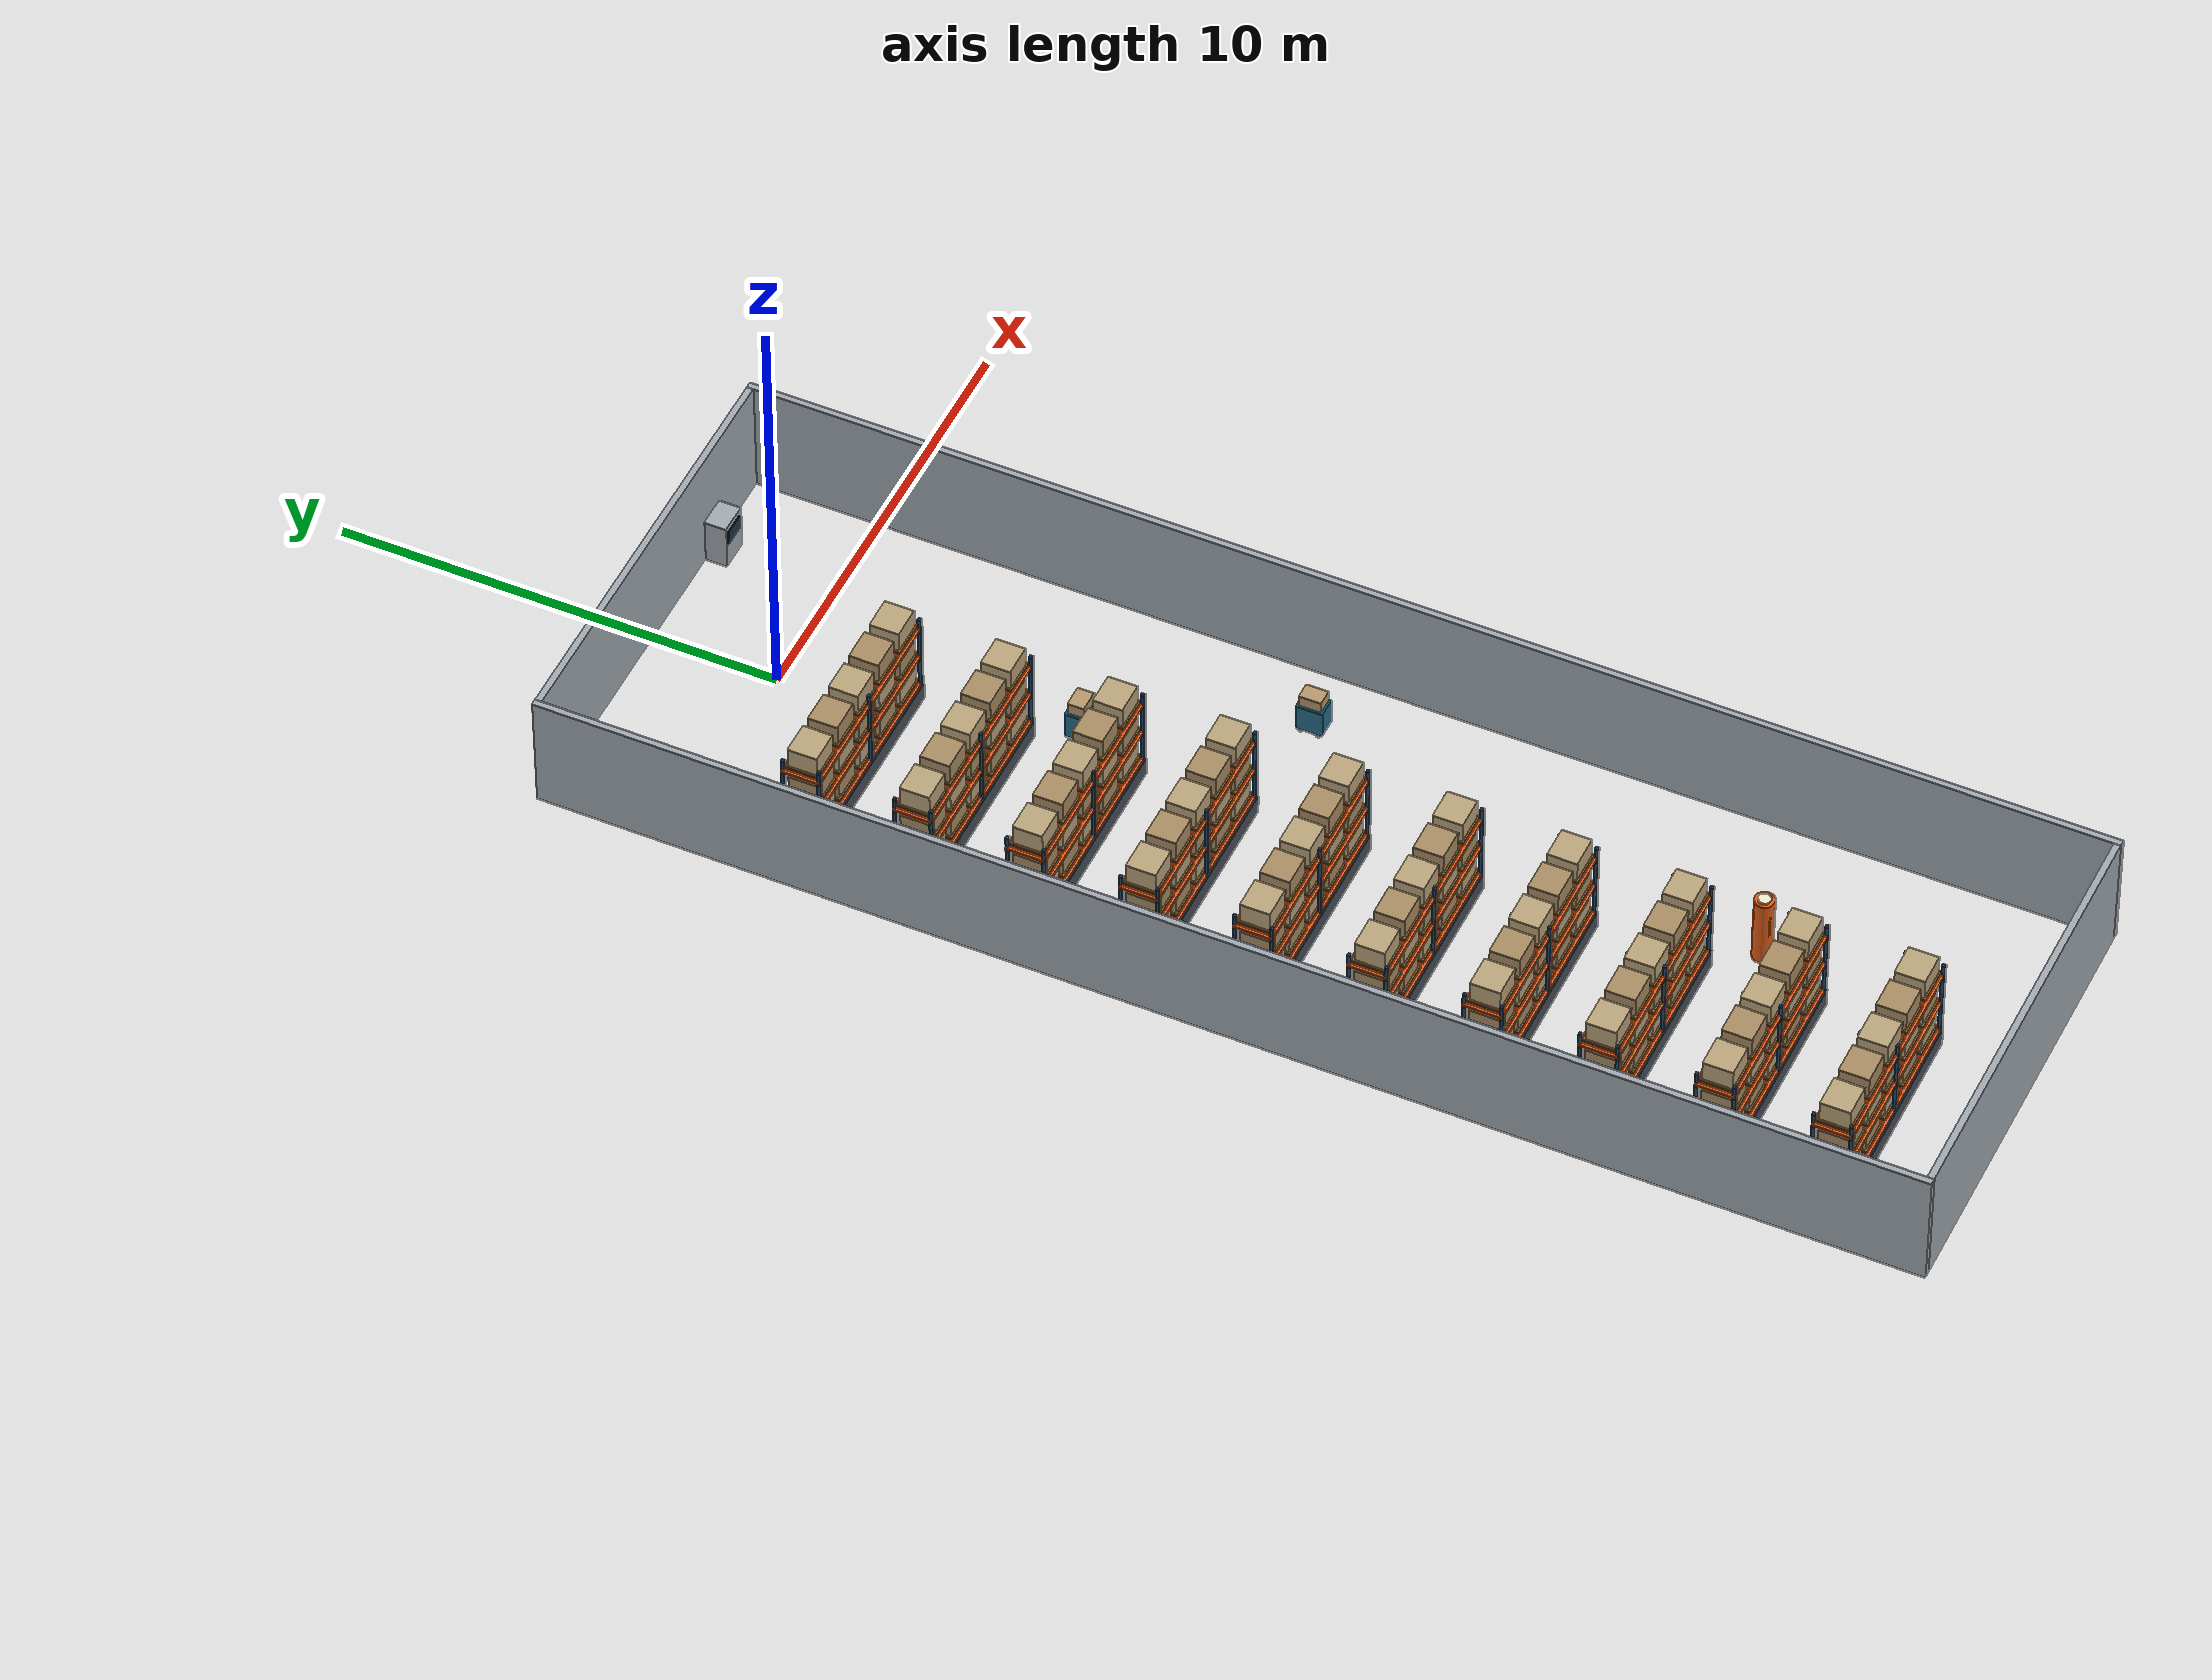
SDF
<sdf version="1.6">
 <world name="warehouse_logistics">
  <gravity>0 0 -9.81</gravity>
  <physics name="warehouse_physics" default="true" type="ode">
   <max_step_size>.002</max_step_size>
   <real_time_factor>1</real_time_factor>
   <real_time_update_rate>500</real_time_update_rate>
  </physics>
  <scene><ambient>.65 .65 .65 1</ambient><background>.80 .84 .88 1</background><shadows>false</shadows></scene>
  <light name="warehouse_sun" type="directional">
   <cast_shadows>false</cast_shadows>
   <diffuse>.85 .85 .85 1</diffuse>
   <specular>.1 .1 .1 1</specular>
   <direction>-.3 -.4 -1</direction>
  </light>
  <plugin name="gazebo_ros_state" filename="libgazebo_ros_state.so">
   <ros><namespace>/gazebo</namespace></ros>
   <update_rate>20</update_rate>
  </plugin>
  <model name="warehouse_ground">
   <static>true</static>
   <link name="floor">
    <collision name="floor_collision">
     <geometry><plane><normal>0 0 1</normal><size>40 70</size></plane></geometry>
    </collision>
   </link>
  </model>
  <model name="warehouse_wall_west">
   <static>true</static>
   <pose>-4.925000000 -12.250000000 0.000000000 0.000000000 0.000000000 0.000000000</pose>
   <link name="structure">
    <collision name="mapped_solid_collision">
     <pose>0.000000000 0.000000000 1.400000000 0.000000000 0.000000000 0.000000000</pose>
     <geometry><box><size>0.150000000 30.500000000 2.800000000</size></box></geometry>
    </collision>
    <visual name="mapped_solid_visual">
     <pose>0.000000000 0.000000000 1.400000000 0.000000000 0.000000000 0.000000000</pose>
     <geometry><box><size>0.150000000 30.500000000 2.800000000</size></box></geometry>
     <material><ambient>.64 .67 .70 1</ambient><diffuse>.64 .67 .70 1</diffuse></material>
    </visual>
   </link>
  </model>
  <model name="warehouse_wall_east">
   <static>true</static>
   <pose>4.925000000 -12.250000000 0.000000000 0.000000000 0.000000000 0.000000000</pose>
   <link name="structure">
    <collision name="mapped_solid_collision">
     <pose>0.000000000 0.000000000 1.400000000 0.000000000 0.000000000 0.000000000</pose>
     <geometry><box><size>0.150000000 30.500000000 2.800000000</size></box></geometry>
    </collision>
    <visual name="mapped_solid_visual">
     <pose>0.000000000 0.000000000 1.400000000 0.000000000 0.000000000 0.000000000</pose>
     <geometry><box><size>0.150000000 30.500000000 2.800000000</size></box></geometry>
     <material><ambient>.64 .67 .70 1</ambient><diffuse>.64 .67 .70 1</diffuse></material>
    </visual>
   </link>
  </model>
  <model name="warehouse_wall_south">
   <static>true</static>
   <pose>0.000000000 -27.425000000 0.000000000 0.000000000 0.000000000 0.000000000</pose>
   <link name="structure">
    <collision name="mapped_solid_collision">
     <pose>0.000000000 0.000000000 1.400000000 0.000000000 0.000000000 0.000000000</pose>
     <geometry><box><size>9.700000000 0.150000000 2.800000000</size></box></geometry>
    </collision>
    <visual name="mapped_solid_visual">
     <pose>0.000000000 0.000000000 1.400000000 0.000000000 0.000000000 0.000000000</pose>
     <geometry><box><size>9.700000000 0.150000000 2.800000000</size></box></geometry>
     <material><ambient>.64 .67 .70 1</ambient><diffuse>.64 .67 .70 1</diffuse></material>
    </visual>
   </link>
  </model>
  <model name="warehouse_wall_north">
   <static>true</static>
   <pose>0.000000000 2.925000000 0.000000000 0.000000000 0.000000000 0.000000000</pose>
   <link name="structure">
    <collision name="mapped_solid_collision">
     <pose>0.000000000 0.000000000 1.400000000 0.000000000 0.000000000 0.000000000</pose>
     <geometry><box><size>9.700000000 0.150000000 2.800000000</size></box></geometry>
    </collision>
    <visual name="mapped_solid_visual">
     <pose>0.000000000 0.000000000 1.400000000 0.000000000 0.000000000 0.000000000</pose>
     <geometry><box><size>9.700000000 0.150000000 2.800000000</size></box></geometry>
     <material><ambient>.64 .67 .70 1</ambient><diffuse>.64 .67 .70 1</diffuse></material>
    </visual>
   </link>
  </model>
  <model name="warehouse_home_dock">
   <static>true</static>
   <pose>2.800000000 2.600000000 0.000000000 0.000000000 0.000000000 0.000000000</pose>
   <link name="structure">
    <collision name="mapped_solid_collision">
     <pose>0.000000000 0.000000000 0.550000000 0.000000000 0.000000000 0.000000000</pose>
     <geometry><box><size>0.700000000 0.500000000 1.100000000</size></box></geometry>
    </collision>
    <visual name="mapped_solid_visual">
     <pose>0.000000000 0.000000000 0.550000000 0.000000000 0.000000000 0.000000000</pose>
     <geometry><box><size>0.700000000 0.500000000 1.100000000</size></box></geometry>
     <material><ambient>.64 .67 .70 1</ambient><diffuse>.64 .67 .70 1</diffuse></material>
    </visual>
    <visual name="charging_panel_visual">
     <pose>0.000000000 -0.251000000 0.780000000 0.000000000 0.000000000 0.000000000</pose>
     <geometry><box><size>0.550000000 0.040000000 0.350000000</size></box></geometry>
     <material><ambient>.12 .20 .26 1</ambient><diffuse>.12 .20 .26 1</diffuse></material>
    </visual>
   </link>
  </model>
  <model name="warehouse_rack_01">
   <static>true</static>
   <pose>-1.600000000 -2.500000000 0.000000000 0.000000000 0.000000000 0.000000000</pose>
   <link name="structure">
    <collision name="mapped_solid_collision">
     <pose>0.000000000 0.000000000 0.225000000 0.000000000 0.000000000 0.000000000</pose>
     <geometry><box><size>4.800000000 0.900000000 0.450000000</size></box></geometry>
    </collision>
    <visual name="mapped_solid_visual">
     <pose>0.000000000 0.000000000 0.225000000 0.000000000 0.000000000 0.000000000</pose>
     <geometry><box><size>4.800000000 0.900000000 0.450000000</size></box></geometry>
     <material><ambient>.27 .31 .35 1</ambient><diffuse>.27 .31 .35 1</diffuse></material>
    </visual>
    <visual name="upright_0_0_visual">
     <pose>-2.340000000 -0.405000000 1.200000000 0.000000000 0.000000000 0.000000000</pose>
     <geometry><box><size>0.075000000 0.075000000 2.400000000</size></box></geometry>
     <material><ambient>.16 .28 .40 1</ambient><diffuse>.16 .28 .40 1</diffuse></material>
    </visual>
    <visual name="upright_0_1_visual">
     <pose>-2.340000000 0.405000000 1.200000000 0.000000000 0.000000000 0.000000000</pose>
     <geometry><box><size>0.075000000 0.075000000 2.400000000</size></box></geometry>
     <material><ambient>.16 .28 .40 1</ambient><diffuse>.16 .28 .40 1</diffuse></material>
    </visual>
    <visual name="upright_1_0_visual">
     <pose>0.000000000 -0.405000000 1.200000000 0.000000000 0.000000000 0.000000000</pose>
     <geometry><box><size>0.075000000 0.075000000 2.400000000</size></box></geometry>
     <material><ambient>.16 .28 .40 1</ambient><diffuse>.16 .28 .40 1</diffuse></material>
    </visual>
    <visual name="upright_1_1_visual">
     <pose>0.000000000 0.405000000 1.200000000 0.000000000 0.000000000 0.000000000</pose>
     <geometry><box><size>0.075000000 0.075000000 2.400000000</size></box></geometry>
     <material><ambient>.16 .28 .40 1</ambient><diffuse>.16 .28 .40 1</diffuse></material>
    </visual>
    <visual name="upright_2_0_visual">
     <pose>2.340000000 -0.405000000 1.200000000 0.000000000 0.000000000 0.000000000</pose>
     <geometry><box><size>0.075000000 0.075000000 2.400000000</size></box></geometry>
     <material><ambient>.16 .28 .40 1</ambient><diffuse>.16 .28 .40 1</diffuse></material>
    </visual>
    <visual name="upright_2_1_visual">
     <pose>2.340000000 0.405000000 1.200000000 0.000000000 0.000000000 0.000000000</pose>
     <geometry><box><size>0.075000000 0.075000000 2.400000000</size></box></geometry>
     <material><ambient>.16 .28 .40 1</ambient><diffuse>.16 .28 .40 1</diffuse></material>
    </visual>
    <visual name="shelf_0_visual">
     <pose>0.000000000 0.000000000 0.500000000 0.000000000 0.000000000 0.000000000</pose>
     <geometry><box><size>4.800000000 0.870000000 0.065000000</size></box></geometry>
     <material><ambient>.92 .36 .10 1</ambient><diffuse>.92 .36 .10 1</diffuse></material>
    </visual>
    <visual name="pallet_0_0_visual">
     <pose>-1.910000000 0.000000000 0.575000000 0.000000000 0.000000000 0.000000000</pose>
     <geometry><box><size>0.820000000 0.750000000 0.080000000</size></box></geometry>
     <material><ambient>.55 .39 .22 1</ambient><diffuse>.55 .39 .22 1</diffuse></material>
    </visual>
    <visual name="load_0_0_visual">
     <pose>-1.910000000 0.000000000 0.855000000 0.000000000 0.000000000 0.000000000</pose>
     <geometry><box><size>0.730000000 0.660000000 0.480000000</size></box></geometry>
     <material><ambient>.74 .65 .49 1</ambient><diffuse>.74 .65 .49 1</diffuse></material>
    </visual>
    <visual name="pallet_0_1_visual">
     <pose>-0.960000000 0.000000000 0.575000000 0.000000000 0.000000000 0.000000000</pose>
     <geometry><box><size>0.820000000 0.750000000 0.080000000</size></box></geometry>
     <material><ambient>.55 .39 .22 1</ambient><diffuse>.55 .39 .22 1</diffuse></material>
    </visual>
    <visual name="load_0_1_visual">
     <pose>-0.960000000 0.000000000 0.855000000 0.000000000 0.000000000 0.000000000</pose>
     <geometry><box><size>0.730000000 0.660000000 0.480000000</size></box></geometry>
     <material><ambient>.67 .56 .40 1</ambient><diffuse>.67 .56 .40 1</diffuse></material>
    </visual>
    <visual name="pallet_0_2_visual">
     <pose>-0.010000000 0.000000000 0.575000000 0.000000000 0.000000000 0.000000000</pose>
     <geometry><box><size>0.820000000 0.750000000 0.080000000</size></box></geometry>
     <material><ambient>.55 .39 .22 1</ambient><diffuse>.55 .39 .22 1</diffuse></material>
    </visual>
    <visual name="load_0_2_visual">
     <pose>-0.010000000 0.000000000 0.855000000 0.000000000 0.000000000 0.000000000</pose>
     <geometry><box><size>0.730000000 0.660000000 0.480000000</size></box></geometry>
     <material><ambient>.74 .65 .49 1</ambient><diffuse>.74 .65 .49 1</diffuse></material>
    </visual>
    <visual name="pallet_0_3_visual">
     <pose>0.940000000 0.000000000 0.575000000 0.000000000 0.000000000 0.000000000</pose>
     <geometry><box><size>0.820000000 0.750000000 0.080000000</size></box></geometry>
     <material><ambient>.55 .39 .22 1</ambient><diffuse>.55 .39 .22 1</diffuse></material>
    </visual>
    <visual name="load_0_3_visual">
     <pose>0.940000000 0.000000000 0.855000000 0.000000000 0.000000000 0.000000000</pose>
     <geometry><box><size>0.730000000 0.660000000 0.480000000</size></box></geometry>
     <material><ambient>.67 .56 .40 1</ambient><diffuse>.67 .56 .40 1</diffuse></material>
    </visual>
    <visual name="pallet_0_4_visual">
     <pose>1.890000000 0.000000000 0.575000000 0.000000000 0.000000000 0.000000000</pose>
     <geometry><box><size>0.820000000 0.750000000 0.080000000</size></box></geometry>
     <material><ambient>.55 .39 .22 1</ambient><diffuse>.55 .39 .22 1</diffuse></material>
    </visual>
    <visual name="load_0_4_visual">
     <pose>1.890000000 0.000000000 0.855000000 0.000000000 0.000000000 0.000000000</pose>
     <geometry><box><size>0.730000000 0.660000000 0.480000000</size></box></geometry>
     <material><ambient>.74 .65 .49 1</ambient><diffuse>.74 .65 .49 1</diffuse></material>
    </visual>
    <visual name="shelf_1_visual">
     <pose>0.000000000 0.000000000 1.300000000 0.000000000 0.000000000 0.000000000</pose>
     <geometry><box><size>4.800000000 0.870000000 0.065000000</size></box></geometry>
     <material><ambient>.92 .36 .10 1</ambient><diffuse>.92 .36 .10 1</diffuse></material>
    </visual>
    <visual name="pallet_1_0_visual">
     <pose>-1.910000000 0.000000000 1.375000000 0.000000000 0.000000000 0.000000000</pose>
     <geometry><box><size>0.820000000 0.750000000 0.080000000</size></box></geometry>
     <material><ambient>.55 .39 .22 1</ambient><diffuse>.55 .39 .22 1</diffuse></material>
    </visual>
    <visual name="load_1_0_visual">
     <pose>-1.910000000 0.000000000 1.655000000 0.000000000 0.000000000 0.000000000</pose>
     <geometry><box><size>0.730000000 0.660000000 0.480000000</size></box></geometry>
     <material><ambient>.67 .56 .40 1</ambient><diffuse>.67 .56 .40 1</diffuse></material>
    </visual>
    <visual name="pallet_1_1_visual">
     <pose>-0.960000000 0.000000000 1.375000000 0.000000000 0.000000000 0.000000000</pose>
     <geometry><box><size>0.820000000 0.750000000 0.080000000</size></box></geometry>
     <material><ambient>.55 .39 .22 1</ambient><diffuse>.55 .39 .22 1</diffuse></material>
    </visual>
    <visual name="load_1_1_visual">
     <pose>-0.960000000 0.000000000 1.655000000 0.000000000 0.000000000 0.000000000</pose>
     <geometry><box><size>0.730000000 0.660000000 0.480000000</size></box></geometry>
     <material><ambient>.74 .65 .49 1</ambient><diffuse>.74 .65 .49 1</diffuse></material>
    </visual>
    <visual name="pallet_1_2_visual">
     <pose>-0.010000000 0.000000000 1.375000000 0.000000000 0.000000000 0.000000000</pose>
     <geometry><box><size>0.820000000 0.750000000 0.080000000</size></box></geometry>
     <material><ambient>.55 .39 .22 1</ambient><diffuse>.55 .39 .22 1</diffuse></material>
    </visual>
    <visual name="load_1_2_visual">
     <pose>-0.010000000 0.000000000 1.655000000 0.000000000 0.000000000 0.000000000</pose>
     <geometry><box><size>0.730000000 0.660000000 0.480000000</size></box></geometry>
     <material><ambient>.67 .56 .40 1</ambient><diffuse>.67 .56 .40 1</diffuse></material>
    </visual>
    <visual name="pallet_1_3_visual">
     <pose>0.940000000 0.000000000 1.375000000 0.000000000 0.000000000 0.000000000</pose>
     <geometry><box><size>0.820000000 0.750000000 0.080000000</size></box></geometry>
     <material><ambient>.55 .39 .22 1</ambient><diffuse>.55 .39 .22 1</diffuse></material>
    </visual>
    <visual name="load_1_3_visual">
     <pose>0.940000000 0.000000000 1.655000000 0.000000000 0.000000000 0.000000000</pose>
     <geometry><box><size>0.730000000 0.660000000 0.480000000</size></box></geometry>
     <material><ambient>.74 .65 .49 1</ambient><diffuse>.74 .65 .49 1</diffuse></material>
    </visual>
    <visual name="pallet_1_4_visual">
     <pose>1.890000000 0.000000000 1.375000000 0.000000000 0.000000000 0.000000000</pose>
     <geometry><box><size>0.820000000 0.750000000 0.080000000</size></box></geometry>
     <material><ambient>.55 .39 .22 1</ambient><diffuse>.55 .39 .22 1</diffuse></material>
    </visual>
    <visual name="load_1_4_visual">
     <pose>1.890000000 0.000000000 1.655000000 0.000000000 0.000000000 0.000000000</pose>
     <geometry><box><size>0.730000000 0.660000000 0.480000000</size></box></geometry>
     <material><ambient>.67 .56 .40 1</ambient><diffuse>.67 .56 .40 1</diffuse></material>
    </visual>
    <visual name="shelf_2_visual">
     <pose>0.000000000 0.000000000 2.100000000 0.000000000 0.000000000 0.000000000</pose>
     <geometry><box><size>4.800000000 0.870000000 0.065000000</size></box></geometry>
     <material><ambient>.92 .36 .10 1</ambient><diffuse>.92 .36 .10 1</diffuse></material>
    </visual>
    <visual name="pallet_2_0_visual">
     <pose>-1.910000000 0.000000000 2.175000000 0.000000000 0.000000000 0.000000000</pose>
     <geometry><box><size>0.820000000 0.750000000 0.080000000</size></box></geometry>
     <material><ambient>.55 .39 .22 1</ambient><diffuse>.55 .39 .22 1</diffuse></material>
    </visual>
    <visual name="load_2_0_visual">
     <pose>-1.910000000 0.000000000 2.455000000 0.000000000 0.000000000 0.000000000</pose>
     <geometry><box><size>0.730000000 0.660000000 0.480000000</size></box></geometry>
     <material><ambient>.74 .65 .49 1</ambient><diffuse>.74 .65 .49 1</diffuse></material>
    </visual>
    <visual name="pallet_2_1_visual">
     <pose>-0.960000000 0.000000000 2.175000000 0.000000000 0.000000000 0.000000000</pose>
     <geometry><box><size>0.820000000 0.750000000 0.080000000</size></box></geometry>
     <material><ambient>.55 .39 .22 1</ambient><diffuse>.55 .39 .22 1</diffuse></material>
    </visual>
    <visual name="load_2_1_visual">
     <pose>-0.960000000 0.000000000 2.455000000 0.000000000 0.000000000 0.000000000</pose>
     <geometry><box><size>0.730000000 0.660000000 0.480000000</size></box></geometry>
     <material><ambient>.67 .56 .40 1</ambient><diffuse>.67 .56 .40 1</diffuse></material>
    </visual>
    <visual name="pallet_2_2_visual">
     <pose>-0.010000000 0.000000000 2.175000000 0.000000000 0.000000000 0.000000000</pose>
     <geometry><box><size>0.820000000 0.750000000 0.080000000</size></box></geometry>
     <material><ambient>.55 .39 .22 1</ambient><diffuse>.55 .39 .22 1</diffuse></material>
    </visual>
    <visual name="load_2_2_visual">
     <pose>-0.010000000 0.000000000 2.455000000 0.000000000 0.000000000 0.000000000</pose>
     <geometry><box><size>0.730000000 0.660000000 0.480000000</size></box></geometry>
     <material><ambient>.74 .65 .49 1</ambient><diffuse>.74 .65 .49 1</diffuse></material>
    </visual>
    <visual name="pallet_2_3_visual">
     <pose>0.940000000 0.000000000 2.175000000 0.000000000 0.000000000 0.000000000</pose>
     <geometry><box><size>0.820000000 0.750000000 0.080000000</size></box></geometry>
     <material><ambient>.55 .39 .22 1</ambient><diffuse>.55 .39 .22 1</diffuse></material>
    </visual>
    <visual name="load_2_3_visual">
     <pose>0.940000000 0.000000000 2.455000000 0.000000000 0.000000000 0.000000000</pose>
     <geometry><box><size>0.730000000 0.660000000 0.480000000</size></box></geometry>
     <material><ambient>.67 .56 .40 1</ambient><diffuse>.67 .56 .40 1</diffuse></material>
    </visual>
    <visual name="pallet_2_4_visual">
     <pose>1.890000000 0.000000000 2.175000000 0.000000000 0.000000000 0.000000000</pose>
     <geometry><box><size>0.820000000 0.750000000 0.080000000</size></box></geometry>
     <material><ambient>.55 .39 .22 1</ambient><diffuse>.55 .39 .22 1</diffuse></material>
    </visual>
    <visual name="load_2_4_visual">
     <pose>1.890000000 0.000000000 2.455000000 0.000000000 0.000000000 0.000000000</pose>
     <geometry><box><size>0.730000000 0.660000000 0.480000000</size></box></geometry>
     <material><ambient>.74 .65 .49 1</ambient><diffuse>.74 .65 .49 1</diffuse></material>
    </visual>
   </link>
  </model>
  <model name="warehouse_rack_02">
   <static>true</static>
   <pose>-1.600000000 -5.000000000 0.000000000 0.000000000 0.000000000 0.000000000</pose>
   <link name="structure">
    <collision name="mapped_solid_collision">
     <pose>0.000000000 0.000000000 0.225000000 0.000000000 0.000000000 0.000000000</pose>
     <geometry><box><size>4.800000000 0.900000000 0.450000000</size></box></geometry>
    </collision>
    <visual name="mapped_solid_visual">
     <pose>0.000000000 0.000000000 0.225000000 0.000000000 0.000000000 0.000000000</pose>
     <geometry><box><size>4.800000000 0.900000000 0.450000000</size></box></geometry>
     <material><ambient>.27 .31 .35 1</ambient><diffuse>.27 .31 .35 1</diffuse></material>
    </visual>
    <visual name="upright_0_0_visual">
     <pose>-2.340000000 -0.405000000 1.200000000 0.000000000 0.000000000 0.000000000</pose>
     <geometry><box><size>0.075000000 0.075000000 2.400000000</size></box></geometry>
     <material><ambient>.16 .28 .40 1</ambient><diffuse>.16 .28 .40 1</diffuse></material>
    </visual>
    <visual name="upright_0_1_visual">
     <pose>-2.340000000 0.405000000 1.200000000 0.000000000 0.000000000 0.000000000</pose>
     <geometry><box><size>0.075000000 0.075000000 2.400000000</size></box></geometry>
     <material><ambient>.16 .28 .40 1</ambient><diffuse>.16 .28 .40 1</diffuse></material>
    </visual>
    <visual name="upright_1_0_visual">
     <pose>0.000000000 -0.405000000 1.200000000 0.000000000 0.000000000 0.000000000</pose>
     <geometry><box><size>0.075000000 0.075000000 2.400000000</size></box></geometry>
     <material><ambient>.16 .28 .40 1</ambient><diffuse>.16 .28 .40 1</diffuse></material>
    </visual>
    <visual name="upright_1_1_visual">
     <pose>0.000000000 0.405000000 1.200000000 0.000000000 0.000000000 0.000000000</pose>
     <geometry><box><size>0.075000000 0.075000000 2.400000000</size></box></geometry>
     <material><ambient>.16 .28 .40 1</ambient><diffuse>.16 .28 .40 1</diffuse></material>
    </visual>
    <visual name="upright_2_0_visual">
     <pose>2.340000000 -0.405000000 1.200000000 0.000000000 0.000000000 0.000000000</pose>
     <geometry><box><size>0.075000000 0.075000000 2.400000000</size></box></geometry>
     <material><ambient>.16 .28 .40 1</ambient><diffuse>.16 .28 .40 1</diffuse></material>
    </visual>
    <visual name="upright_2_1_visual">
     <pose>2.340000000 0.405000000 1.200000000 0.000000000 0.000000000 0.000000000</pose>
     <geometry><box><size>0.075000000 0.075000000 2.400000000</size></box></geometry>
     <material><ambient>.16 .28 .40 1</ambient><diffuse>.16 .28 .40 1</diffuse></material>
    </visual>
    <visual name="shelf_0_visual">
     <pose>0.000000000 0.000000000 0.500000000 0.000000000 0.000000000 0.000000000</pose>
     <geometry><box><size>4.800000000 0.870000000 0.065000000</size></box></geometry>
     <material><ambient>.92 .36 .10 1</ambient><diffuse>.92 .36 .10 1</diffuse></material>
    </visual>
    <visual name="pallet_0_0_visual">
     <pose>-1.910000000 0.000000000 0.575000000 0.000000000 0.000000000 0.000000000</pose>
     <geometry><box><size>0.820000000 0.750000000 0.080000000</size></box></geometry>
     <material><ambient>.55 .39 .22 1</ambient><diffuse>.55 .39 .22 1</diffuse></material>
    </visual>
    <visual name="load_0_0_visual">
     <pose>-1.910000000 0.000000000 0.855000000 0.000000000 0.000000000 0.000000000</pose>
     <geometry><box><size>0.730000000 0.660000000 0.480000000</size></box></geometry>
     <material><ambient>.74 .65 .49 1</ambient><diffuse>.74 .65 .49 1</diffuse></material>
    </visual>
    <visual name="pallet_0_1_visual">
     <pose>-0.960000000 0.000000000 0.575000000 0.000000000 0.000000000 0.000000000</pose>
     <geometry><box><size>0.820000000 0.750000000 0.080000000</size></box></geometry>
     <material><ambient>.55 .39 .22 1</ambient><diffuse>.55 .39 .22 1</diffuse></material>
    </visual>
    <visual name="load_0_1_visual">
     <pose>-0.960000000 0.000000000 0.855000000 0.000000000 0.000000000 0.000000000</pose>
     <geometry><box><size>0.730000000 0.660000000 0.480000000</size></box></geometry>
     <material><ambient>.67 .56 .40 1</ambient><diffuse>.67 .56 .40 1</diffuse></material>
    </visual>
    <visual name="pallet_0_2_visual">
     <pose>-0.010000000 0.000000000 0.575000000 0.000000000 0.000000000 0.000000000</pose>
     <geometry><box><size>0.820000000 0.750000000 0.080000000</size></box></geometry>
     <material><ambient>.55 .39 .22 1</ambient><diffuse>.55 .39 .22 1</diffuse></material>
    </visual>
    <visual name="load_0_2_visual">
     <pose>-0.010000000 0.000000000 0.855000000 0.000000000 0.000000000 0.000000000</pose>
     <geometry><box><size>0.730000000 0.660000000 0.480000000</size></box></geometry>
     <material><ambient>.74 .65 .49 1</ambient><diffuse>.74 .65 .49 1</diffuse></material>
    </visual>
    <visual name="pallet_0_3_visual">
     <pose>0.940000000 0.000000000 0.575000000 0.000000000 0.000000000 0.000000000</pose>
     <geometry><box><size>0.820000000 0.750000000 0.080000000</size></box></geometry>
     <material><ambient>.55 .39 .22 1</ambient><diffuse>.55 .39 .22 1</diffuse></material>
    </visual>
    <visual name="load_0_3_visual">
     <pose>0.940000000 0.000000000 0.855000000 0.000000000 0.000000000 0.000000000</pose>
     <geometry><box><size>0.730000000 0.660000000 0.480000000</size></box></geometry>
     <material><ambient>.67 .56 .40 1</ambient><diffuse>.67 .56 .40 1</diffuse></material>
    </visual>
    <visual name="pallet_0_4_visual">
     <pose>1.890000000 0.000000000 0.575000000 0.000000000 0.000000000 0.000000000</pose>
     <geometry><box><size>0.820000000 0.750000000 0.080000000</size></box></geometry>
     <material><ambient>.55 .39 .22 1</ambient><diffuse>.55 .39 .22 1</diffuse></material>
    </visual>
    <visual name="load_0_4_visual">
     <pose>1.890000000 0.000000000 0.855000000 0.000000000 0.000000000 0.000000000</pose>
     <geometry><box><size>0.730000000 0.660000000 0.480000000</size></box></geometry>
     <material><ambient>.74 .65 .49 1</ambient><diffuse>.74 .65 .49 1</diffuse></material>
    </visual>
    <visual name="shelf_1_visual">
     <pose>0.000000000 0.000000000 1.300000000 0.000000000 0.000000000 0.000000000</pose>
     <geometry><box><size>4.800000000 0.870000000 0.065000000</size></box></geometry>
     <material><ambient>.92 .36 .10 1</ambient><diffuse>.92 .36 .10 1</diffuse></material>
    </visual>
    <visual name="pallet_1_0_visual">
     <pose>-1.910000000 0.000000000 1.375000000 0.000000000 0.000000000 0.000000000</pose>
     <geometry><box><size>0.820000000 0.750000000 0.080000000</size></box></geometry>
     <material><ambient>.55 .39 .22 1</ambient><diffuse>.55 .39 .22 1</diffuse></material>
    </visual>
    <visual name="load_1_0_visual">
     <pose>-1.910000000 0.000000000 1.655000000 0.000000000 0.000000000 0.000000000</pose>
     <geometry><box><size>0.730000000 0.660000000 0.480000000</size></box></geometry>
     <material><ambient>.67 .56 .40 1</ambient><diffuse>.67 .56 .40 1</diffuse></material>
    </visual>
    <visual name="pallet_1_1_visual">
     <pose>-0.960000000 0.000000000 1.375000000 0.000000000 0.000000000 0.000000000</pose>
     <geometry><box><size>0.820000000 0.750000000 0.080000000</size></box></geometry>
     <material><ambient>.55 .39 .22 1</ambient><diffuse>.55 .39 .22 1</diffuse></material>
    </visual>
    <visual name="load_1_1_visual">
     <pose>-0.960000000 0.000000000 1.655000000 0.000000000 0.000000000 0.000000000</pose>
     <geometry><box><size>0.730000000 0.660000000 0.480000000</size></box></geometry>
     <material><ambient>.74 .65 .49 1</ambient><diffuse>.74 .65 .49 1</diffuse></material>
    </visual>
    <visual name="pallet_1_2_visual">
     <pose>-0.010000000 0.000000000 1.375000000 0.000000000 0.000000000 0.000000000</pose>
     <geometry><box><size>0.820000000 0.750000000 0.080000000</size></box></geometry>
     <material><ambient>.55 .39 .22 1</ambient><diffuse>.55 .39 .22 1</diffuse></material>
    </visual>
    <visual name="load_1_2_visual">
     <pose>-0.010000000 0.000000000 1.655000000 0.000000000 0.000000000 0.000000000</pose>
     <geometry><box><size>0.730000000 0.660000000 0.480000000</size></box></geometry>
     <material><ambient>.67 .56 .40 1</ambient><diffuse>.67 .56 .40 1</diffuse></material>
    </visual>
    <visual name="pallet_1_3_visual">
     <pose>0.940000000 0.000000000 1.375000000 0.000000000 0.000000000 0.000000000</pose>
     <geometry><box><size>0.820000000 0.750000000 0.080000000</size></box></geometry>
     <material><ambient>.55 .39 .22 1</ambient><diffuse>.55 .39 .22 1</diffuse></material>
    </visual>
    <visual name="load_1_3_visual">
     <pose>0.940000000 0.000000000 1.655000000 0.000000000 0.000000000 0.000000000</pose>
     <geometry><box><size>0.730000000 0.660000000 0.480000000</size></box></geometry>
     <material><ambient>.74 .65 .49 1</ambient><diffuse>.74 .65 .49 1</diffuse></material>
    </visual>
    <visual name="pallet_1_4_visual">
     <pose>1.890000000 0.000000000 1.375000000 0.000000000 0.000000000 0.000000000</pose>
     <geometry><box><size>0.820000000 0.750000000 0.080000000</size></box></geometry>
     <material><ambient>.55 .39 .22 1</ambient><diffuse>.55 .39 .22 1</diffuse></material>
    </visual>
    <visual name="load_1_4_visual">
     <pose>1.890000000 0.000000000 1.655000000 0.000000000 0.000000000 0.000000000</pose>
     <geometry><box><size>0.730000000 0.660000000 0.480000000</size></box></geometry>
     <material><ambient>.67 .56 .40 1</ambient><diffuse>.67 .56 .40 1</diffuse></material>
    </visual>
    <visual name="shelf_2_visual">
     <pose>0.000000000 0.000000000 2.100000000 0.000000000 0.000000000 0.000000000</pose>
     <geometry><box><size>4.800000000 0.870000000 0.065000000</size></box></geometry>
     <material><ambient>.92 .36 .10 1</ambient><diffuse>.92 .36 .10 1</diffuse></material>
    </visual>
    <visual name="pallet_2_0_visual">
     <pose>-1.910000000 0.000000000 2.175000000 0.000000000 0.000000000 0.000000000</pose>
     <geometry><box><size>0.820000000 0.750000000 0.080000000</size></box></geometry>
     <material><ambient>.55 .39 .22 1</ambient><diffuse>.55 .39 .22 1</diffuse></material>
    </visual>
    <visual name="load_2_0_visual">
     <pose>-1.910000000 0.000000000 2.455000000 0.000000000 0.000000000 0.000000000</pose>
     <geometry><box><size>0.730000000 0.660000000 0.480000000</size></box></geometry>
     <material><ambient>.74 .65 .49 1</ambient><diffuse>.74 .65 .49 1</diffuse></material>
    </visual>
    <visual name="pallet_2_1_visual">
     <pose>-0.960000000 0.000000000 2.175000000 0.000000000 0.000000000 0.000000000</pose>
     <geometry><box><size>0.820000000 0.750000000 0.080000000</size></box></geometry>
     <material><ambient>.55 .39 .22 1</ambient><diffuse>.55 .39 .22 1</diffuse></material>
    </visual>
    <visual name="load_2_1_visual">
     <pose>-0.960000000 0.000000000 2.455000000 0.000000000 0.000000000 0.000000000</pose>
     <geometry><box><size>0.730000000 0.660000000 0.480000000</size></box></geometry>
     <material><ambient>.67 .56 .40 1</ambient><diffuse>.67 .56 .40 1</diffuse></material>
    </visual>
    <visual name="pallet_2_2_visual">
     <pose>-0.010000000 0.000000000 2.175000000 0.000000000 0.000000000 0.000000000</pose>
     <geometry><box><size>0.820000000 0.750000000 0.080000000</size></box></geometry>
     <material><ambient>.55 .39 .22 1</ambient><diffuse>.55 .39 .22 1</diffuse></material>
    </visual>
    <visual name="load_2_2_visual">
     <pose>-0.010000000 0.000000000 2.455000000 0.000000000 0.000000000 0.000000000</pose>
     <geometry><box><size>0.730000000 0.660000000 0.480000000</size></box></geometry>
     <material><ambient>.74 .65 .49 1</ambient><diffuse>.74 .65 .49 1</diffuse></material>
    </visual>
    <visual name="pallet_2_3_visual">
     <pose>0.940000000 0.000000000 2.175000000 0.000000000 0.000000000 0.000000000</pose>
     <geometry><box><size>0.820000000 0.750000000 0.080000000</size></box></geometry>
     <material><ambient>.55 .39 .22 1</ambient><diffuse>.55 .39 .22 1</diffuse></material>
    </visual>
    <visual name="load_2_3_visual">
     <pose>0.940000000 0.000000000 2.455000000 0.000000000 0.000000000 0.000000000</pose>
     <geometry><box><size>0.730000000 0.660000000 0.480000000</size></box></geometry>
     <material><ambient>.67 .56 .40 1</ambient><diffuse>.67 .56 .40 1</diffuse></material>
    </visual>
    <visual name="pallet_2_4_visual">
     <pose>1.890000000 0.000000000 2.175000000 0.000000000 0.000000000 0.000000000</pose>
     <geometry><box><size>0.820000000 0.750000000 0.080000000</size></box></geometry>
     <material><ambient>.55 .39 .22 1</ambient><diffuse>.55 .39 .22 1</diffuse></material>
    </visual>
    <visual name="load_2_4_visual">
     <pose>1.890000000 0.000000000 2.455000000 0.000000000 0.000000000 0.000000000</pose>
     <geometry><box><size>0.730000000 0.660000000 0.480000000</size></box></geometry>
     <material><ambient>.74 .65 .49 1</ambient><diffuse>.74 .65 .49 1</diffuse></material>
    </visual>
   </link>
  </model>
  <model name="warehouse_rack_03">
   <static>true</static>
   <pose>-1.600000000 -7.500000000 0.000000000 0.000000000 0.000000000 0.000000000</pose>
   <link name="structure">
    <collision name="mapped_solid_collision">
     <pose>0.000000000 0.000000000 0.225000000 0.000000000 0.000000000 0.000000000</pose>
     <geometry><box><size>4.800000000 0.900000000 0.450000000</size></box></geometry>
    </collision>
    <visual name="mapped_solid_visual">
     <pose>0.000000000 0.000000000 0.225000000 0.000000000 0.000000000 0.000000000</pose>
     <geometry><box><size>4.800000000 0.900000000 0.450000000</size></box></geometry>
     <material><ambient>.27 .31 .35 1</ambient><diffuse>.27 .31 .35 1</diffuse></material>
    </visual>
    <visual name="upright_0_0_visual">
     <pose>-2.340000000 -0.405000000 1.200000000 0.000000000 0.000000000 0.000000000</pose>
     <geometry><box><size>0.075000000 0.075000000 2.400000000</size></box></geometry>
     <material><ambient>.16 .28 .40 1</ambient><diffuse>.16 .28 .40 1</diffuse></material>
    </visual>
    <visual name="upright_0_1_visual">
     <pose>-2.340000000 0.405000000 1.200000000 0.000000000 0.000000000 0.000000000</pose>
     <geometry><box><size>0.075000000 0.075000000 2.400000000</size></box></geometry>
     <material><ambient>.16 .28 .40 1</ambient><diffuse>.16 .28 .40 1</diffuse></material>
    </visual>
    <visual name="upright_1_0_visual">
     <pose>0.000000000 -0.405000000 1.200000000 0.000000000 0.000000000 0.000000000</pose>
     <geometry><box><size>0.075000000 0.075000000 2.400000000</size></box></geometry>
     <material><ambient>.16 .28 .40 1</ambient><diffuse>.16 .28 .40 1</diffuse></material>
    </visual>
    <visual name="upright_1_1_visual">
     <pose>0.000000000 0.405000000 1.200000000 0.000000000 0.000000000 0.000000000</pose>
     <geometry><box><size>0.075000000 0.075000000 2.400000000</size></box></geometry>
     <material><ambient>.16 .28 .40 1</ambient><diffuse>.16 .28 .40 1</diffuse></material>
    </visual>
    <visual name="upright_2_0_visual">
     <pose>2.340000000 -0.405000000 1.200000000 0.000000000 0.000000000 0.000000000</pose>
     <geometry><box><size>0.075000000 0.075000000 2.400000000</size></box></geometry>
     <material><ambient>.16 .28 .40 1</ambient><diffuse>.16 .28 .40 1</diffuse></material>
    </visual>
    <visual name="upright_2_1_visual">
     <pose>2.340000000 0.405000000 1.200000000 0.000000000 0.000000000 0.000000000</pose>
     <geometry><box><size>0.075000000 0.075000000 2.400000000</size></box></geometry>
     <material><ambient>.16 .28 .40 1</ambient><diffuse>.16 .28 .40 1</diffuse></material>
    </visual>
    <visual name="shelf_0_visual">
     <pose>0.000000000 0.000000000 0.500000000 0.000000000 0.000000000 0.000000000</pose>
     <geometry><box><size>4.800000000 0.870000000 0.065000000</size></box></geometry>
     <material><ambient>.92 .36 .10 1</ambient><diffuse>.92 .36 .10 1</diffuse></material>
    </visual>
    <visual name="pallet_0_0_visual">
     <pose>-1.910000000 0.000000000 0.575000000 0.000000000 0.000000000 0.000000000</pose>
     <geometry><box><size>0.820000000 0.750000000 0.080000000</size></box></geometry>
     <material><ambient>.55 .39 .22 1</ambient><diffuse>.55 .39 .22 1</diffuse></material>
    </visual>
    <visual name="load_0_0_visual">
     <pose>-1.910000000 0.000000000 0.855000000 0.000000000 0.000000000 0.000000000</pose>
     <geometry><box><size>0.730000000 0.660000000 0.480000000</size></box></geometry>
     <material><ambient>.74 .65 .49 1</ambient><diffuse>.74 .65 .49 1</diffuse></material>
    </visual>
    <visual name="pallet_0_1_visual">
     <pose>-0.960000000 0.000000000 0.575000000 0.000000000 0.000000000 0.000000000</pose>
     <geometry><box><size>0.820000000 0.750000000 0.080000000</size></box></geometry>
     <material><ambient>.55 .39 .22 1</ambient><diffuse>.55 .39 .22 1</diffuse></material>
    </visual>
    <visual name="load_0_1_visual">
     <pose>-0.960000000 0.000000000 0.855000000 0.000000000 0.000000000 0.000000000</pose>
     <geometry><box><size>0.730000000 0.660000000 0.480000000</size></box></geometry>
     <material><ambient>.67 .56 .40 1</ambient><diffuse>.67 .56 .40 1</diffuse></material>
    </visual>
    <visual name="pallet_0_2_visual">
     <pose>-0.010000000 0.000000000 0.575000000 0.000000000 0.000000000 0.000000000</pose>
     <geometry><box><size>0.820000000 0.750000000 0.080000000</size></box></geometry>
     <material><ambient>.55 .39 .22 1</ambient><diffuse>.55 .39 .22 1</diffuse></material>
    </visual>
    <visual name="load_0_2_visual">
     <pose>-0.010000000 0.000000000 0.855000000 0.000000000 0.000000000 0.000000000</pose>
     <geometry><box><size>0.730000000 0.660000000 0.480000000</size></box></geometry>
     <material><ambient>.74 .65 .49 1</ambient><diffuse>.74 .65 .49 1</diffuse></material>
    </visual>
    <visual name="pallet_0_3_visual">
     <pose>0.940000000 0.000000000 0.575000000 0.000000000 0.000000000 0.000000000</pose>
     <geometry><box><size>0.820000000 0.750000000 0.080000000</size></box></geometry>
     <material><ambient>.55 .39 .22 1</ambient><diffuse>.55 .39 .22 1</diffuse></material>
    </visual>
    <visual name="load_0_3_visual">
     <pose>0.940000000 0.000000000 0.855000000 0.000000000 0.000000000 0.000000000</pose>
     <geometry><box><size>0.730000000 0.660000000 0.480000000</size></box></geometry>
     <material><ambient>.67 .56 .40 1</ambient><diffuse>.67 .56 .40 1</diffuse></material>
    </visual>
    <visual name="pallet_0_4_visual">
     <pose>1.890000000 0.000000000 0.575000000 0.000000000 0.000000000 0.000000000</pose>
     <geometry><box><size>0.820000000 0.750000000 0.080000000</size></box></geometry>
     <material><ambient>.55 .39 .22 1</ambient><diffuse>.55 .39 .22 1</diffuse></material>
    </visual>
    <visual name="load_0_4_visual">
     <pose>1.890000000 0.000000000 0.855000000 0.000000000 0.000000000 0.000000000</pose>
     <geometry><box><size>0.730000000 0.660000000 0.480000000</size></box></geometry>
     <material><ambient>.74 .65 .49 1</ambient><diffuse>.74 .65 .49 1</diffuse></material>
    </visual>
    <visual name="shelf_1_visual">
     <pose>0.000000000 0.000000000 1.300000000 0.000000000 0.000000000 0.000000000</pose>
     <geometry><box><size>4.800000000 0.870000000 0.065000000</size></box></geometry>
     <material><ambient>.92 .36 .10 1</ambient><diffuse>.92 .36 .10 1</diffuse></material>
    </visual>
    <visual name="pallet_1_0_visual">
     <pose>-1.910000000 0.000000000 1.375000000 0.000000000 0.000000000 0.000000000</pose>
     <geometry><box><size>0.820000000 0.750000000 0.080000000</size></box></geometry>
     <material><ambient>.55 .39 .22 1</ambient><diffuse>.55 .39 .22 1</diffuse></material>
    </visual>
    <visual name="load_1_0_visual">
     <pose>-1.910000000 0.000000000 1.655000000 0.000000000 0.000000000 0.000000000</pose>
     <geometry><box><size>0.730000000 0.660000000 0.480000000</size></box></geometry>
     <material><ambient>.67 .56 .40 1</ambient><diffuse>.67 .56 .40 1</diffuse></material>
    </visual>
    <visual name="pallet_1_1_visual">
     <pose>-0.960000000 0.000000000 1.375000000 0.000000000 0.000000000 0.000000000</pose>
     <geometry><box><size>0.820000000 0.750000000 0.080000000</size></box></geometry>
     <material><ambient>.55 .39 .22 1</ambient><diffuse>.55 .39 .22 1</diffuse></material>
    </visual>
    <visual name="load_1_1_visual">
     <pose>-0.960000000 0.000000000 1.655000000 0.000000000 0.000000000 0.000000000</pose>
     <geometry><box><size>0.730000000 0.660000000 0.480000000</size></box></geometry>
     <material><ambient>.74 .65 .49 1</ambient><diffuse>.74 .65 .49 1</diffuse></material>
    </visual>
    <visual name="pallet_1_2_visual">
     <pose>-0.010000000 0.000000000 1.375000000 0.000000000 0.000000000 0.000000000</pose>
     <geometry><box><size>0.820000000 0.750000000 0.080000000</size></box></geometry>
     <material><ambient>.55 .39 .22 1</ambient><diffuse>.55 .39 .22 1</diffuse></material>
    </visual>
    <visual name="load_1_2_visual">
     <pose>-0.010000000 0.000000000 1.655000000 0.000000000 0.000000000 0.000000000</pose>
     <geometry><box><size>0.730000000 0.660000000 0.480000000</size></box></geometry>
     <material><ambient>.67 .56 .40 1</ambient><diffuse>.67 .56 .40 1</diffuse></material>
    </visual>
    <visual name="pallet_1_3_visual">
     <pose>0.940000000 0.000000000 1.375000000 0.000000000 0.000000000 0.000000000</pose>
     <geometry><box><size>0.820000000 0.750000000 0.080000000</size></box></geometry>
     <material><ambient>.55 .39 .22 1</ambient><diffuse>.55 .39 .22 1</diffuse></material>
    </visual>
    <visual name="load_1_3_visual">
     <pose>0.940000000 0.000000000 1.655000000 0.000000000 0.000000000 0.000000000</pose>
     <geometry><box><size>0.730000000 0.660000000 0.480000000</size></box></geometry>
     <material><ambient>.74 .65 .49 1</ambient><diffuse>.74 .65 .49 1</diffuse></material>
    </visual>
    <visual name="pallet_1_4_visual">
     <pose>1.890000000 0.000000000 1.375000000 0.000000000 0.000000000 0.000000000</pose>
     <geometry><box><size>0.820000000 0.750000000 0.080000000</size></box></geometry>
     <material><ambient>.55 .39 .22 1</ambient><diffuse>.55 .39 .22 1</diffuse></material>
    </visual>
    <visual name="load_1_4_visual">
     <pose>1.890000000 0.000000000 1.655000000 0.000000000 0.000000000 0.000000000</pose>
     <geometry><box><size>0.730000000 0.660000000 0.480000000</size></box></geometry>
     <material><ambient>.67 .56 .40 1</ambient><diffuse>.67 .56 .40 1</diffuse></material>
    </visual>
    <visual name="shelf_2_visual">
     <pose>0.000000000 0.000000000 2.100000000 0.000000000 0.000000000 0.000000000</pose>
     <geometry><box><size>4.800000000 0.870000000 0.065000000</size></box></geometry>
     <material><ambient>.92 .36 .10 1</ambient><diffuse>.92 .36 .10 1</diffuse></material>
    </visual>
    <visual name="pallet_2_0_visual">
     <pose>-1.910000000 0.000000000 2.175000000 0.000000000 0.000000000 0.000000000</pose>
     <geometry><box><size>0.820000000 0.750000000 0.080000000</size></box></geometry>
     <material><ambient>.55 .39 .22 1</ambient><diffuse>.55 .39 .22 1</diffuse></material>
    </visual>
    <visual name="load_2_0_visual">
     <pose>-1.910000000 0.000000000 2.455000000 0.000000000 0.000000000 0.000000000</pose>
     <geometry><box><size>0.730000000 0.660000000 0.480000000</size></box></geometry>
     <material><ambient>.74 .65 .49 1</ambient><diffuse>.74 .65 .49 1</diffuse></material>
    </visual>
    <visual name="pallet_2_1_visual">
     <pose>-0.960000000 0.000000000 2.175000000 0.000000000 0.000000000 0.000000000</pose>
     <geometry><box><size>0.820000000 0.750000000 0.080000000</size></box></geometry>
     <material><ambient>.55 .39 .22 1</ambient><diffuse>.55 .39 .22 1</diffuse></material>
    </visual>
    <visual name="load_2_1_visual">
     <pose>-0.960000000 0.000000000 2.455000000 0.000000000 0.000000000 0.000000000</pose>
     <geometry><box><size>0.730000000 0.660000000 0.480000000</size></box></geometry>
     <material><ambient>.67 .56 .40 1</ambient><diffuse>.67 .56 .40 1</diffuse></material>
    </visual>
    <visual name="pallet_2_2_visual">
     <pose>-0.010000000 0.000000000 2.175000000 0.000000000 0.000000000 0.000000000</pose>
     <geometry><box><size>0.820000000 0.750000000 0.080000000</size></box></geometry>
     <material><ambient>.55 .39 .22 1</ambient><diffuse>.55 .39 .22 1</diffuse></material>
    </visual>
    <visual name="load_2_2_visual">
     <pose>-0.010000000 0.000000000 2.455000000 0.000000000 0.000000000 0.000000000</pose>
     <geometry><box><size>0.730000000 0.660000000 0.480000000</size></box></geometry>
     <material><ambient>.74 .65 .49 1</ambient><diffuse>.74 .65 .49 1</diffuse></material>
    </visual>
    <visual name="pallet_2_3_visual">
     <pose>0.940000000 0.000000000 2.175000000 0.000000000 0.000000000 0.000000000</pose>
     <geometry><box><size>0.820000000 0.750000000 0.080000000</size></box></geometry>
     <material><ambient>.55 .39 .22 1</ambient><diffuse>.55 .39 .22 1</diffuse></material>
    </visual>
    <visual name="load_2_3_visual">
     <pose>0.940000000 0.000000000 2.455000000 0.000000000 0.000000000 0.000000000</pose>
     <geometry><box><size>0.730000000 0.660000000 0.480000000</size></box></geometry>
     <material><ambient>.67 .56 .40 1</ambient><diffuse>.67 .56 .40 1</diffuse></material>
    </visual>
    <visual name="pallet_2_4_visual">
     <pose>1.890000000 0.000000000 2.175000000 0.000000000 0.000000000 0.000000000</pose>
     <geometry><box><size>0.820000000 0.750000000 0.080000000</size></box></geometry>
     <material><ambient>.55 .39 .22 1</ambient><diffuse>.55 .39 .22 1</diffuse></material>
    </visual>
    <visual name="load_2_4_visual">
     <pose>1.890000000 0.000000000 2.455000000 0.000000000 0.000000000 0.000000000</pose>
     <geometry><box><size>0.730000000 0.660000000 0.480000000</size></box></geometry>
     <material><ambient>.74 .65 .49 1</ambient><diffuse>.74 .65 .49 1</diffuse></material>
    </visual>
   </link>
  </model>
  <model name="warehouse_rack_04">
   <static>true</static>
   <pose>-1.600000000 -10.000000000 0.000000000 0.000000000 0.000000000 0.000000000</pose>
   <link name="structure">
    <collision name="mapped_solid_collision">
     <pose>0.000000000 0.000000000 0.225000000 0.000000000 0.000000000 0.000000000</pose>
     <geometry><box><size>4.800000000 0.900000000 0.450000000</size></box></geometry>
    </collision>
    <visual name="mapped_solid_visual">
     <pose>0.000000000 0.000000000 0.225000000 0.000000000 0.000000000 0.000000000</pose>
     <geometry><box><size>4.800000000 0.900000000 0.450000000</size></box></geometry>
     <material><ambient>.27 .31 .35 1</ambient><diffuse>.27 .31 .35 1</diffuse></material>
    </visual>
    <visual name="upright_0_0_visual">
     <pose>-2.340000000 -0.405000000 1.200000000 0.000000000 0.000000000 0.000000000</pose>
     <geometry><box><size>0.075000000 0.075000000 2.400000000</size></box></geometry>
     <material><ambient>.16 .28 .40 1</ambient><diffuse>.16 .28 .40 1</diffuse></material>
    </visual>
    <visual name="upright_0_1_visual">
     <pose>-2.340000000 0.405000000 1.200000000 0.000000000 0.000000000 0.000000000</pose>
     <geometry><box><size>0.075000000 0.075000000 2.400000000</size></box></geometry>
     <material><ambient>.16 .28 .40 1</ambient><diffuse>.16 .28 .40 1</diffuse></material>
    </visual>
    <visual name="upright_1_0_visual">
     <pose>0.000000000 -0.405000000 1.200000000 0.000000000 0.000000000 0.000000000</pose>
     <geometry><box><size>0.075000000 0.075000000 2.400000000</size></box></geometry>
     <material><ambient>.16 .28 .40 1</ambient><diffuse>.16 .28 .40 1</diffuse></material>
    </visual>
    <visual name="upright_1_1_visual">
     <pose>0.000000000 0.405000000 1.200000000 0.000000000 0.000000000 0.000000000</pose>
     <geometry><box><size>0.075000000 0.075000000 2.400000000</size></box></geometry>
     <material><ambient>.16 .28 .40 1</ambient><diffuse>.16 .28 .40 1</diffuse></material>
    </visual>
    <visual name="upright_2_0_visual">
     <pose>2.340000000 -0.405000000 1.200000000 0.000000000 0.000000000 0.000000000</pose>
     <geometry><box><size>0.075000000 0.075000000 2.400000000</size></box></geometry>
     <material><ambient>.16 .28 .40 1</ambient><diffuse>.16 .28 .40 1</diffuse></material>
    </visual>
    <visual name="upright_2_1_visual">
     <pose>2.340000000 0.405000000 1.200000000 0.000000000 0.000000000 0.000000000</pose>
     <geometry><box><size>0.075000000 0.075000000 2.400000000</size></box></geometry>
     <material><ambient>.16 .28 .40 1</ambient><diffuse>.16 .28 .40 1</diffuse></material>
    </visual>
    <visual name="shelf_0_visual">
     <pose>0.000000000 0.000000000 0.500000000 0.000000000 0.000000000 0.000000000</pose>
     <geometry><box><size>4.800000000 0.870000000 0.065000000</size></box></geometry>
     <material><ambient>.92 .36 .10 1</ambient><diffuse>.92 .36 .10 1</diffuse></material>
    </visual>
    <visual name="pallet_0_0_visual">
     <pose>-1.910000000 0.000000000 0.575000000 0.000000000 0.000000000 0.000000000</pose>
     <geometry><box><size>0.820000000 0.750000000 0.080000000</size></box></geometry>
     <material><ambient>.55 .39 .22 1</ambient><diffuse>.55 .39 .22 1</diffuse></material>
    </visual>
    <visual name="load_0_0_visual">
     <pose>-1.910000000 0.000000000 0.855000000 0.000000000 0.000000000 0.000000000</pose>
     <geometry><box><size>0.730000000 0.660000000 0.480000000</size></box></geometry>
     <material><ambient>.74 .65 .49 1</ambient><diffuse>.74 .65 .49 1</diffuse></material>
    </visual>
    <visual name="pallet_0_1_visual">
     <pose>-0.960000000 0.000000000 0.575000000 0.000000000 0.000000000 0.000000000</pose>
     <geometry><box><size>0.820000000 0.750000000 0.080000000</size></box></geometry>
     <material><ambient>.55 .39 .22 1</ambient><diffuse>.55 .39 .22 1</diffuse></material>
    </visual>
    <visual name="load_0_1_visual">
     <pose>-0.960000000 0.000000000 0.855000000 0.000000000 0.000000000 0.000000000</pose>
     <geometry><box><size>0.730000000 0.660000000 0.480000000</size></box></geometry>
     <material><ambient>.67 .56 .40 1</ambient><diffuse>.67 .56 .40 1</diffuse></material>
    </visual>
    <visual name="pallet_0_2_visual">
     <pose>-0.010000000 0.000000000 0.575000000 0.000000000 0.000000000 0.000000000</pose>
     <geometry><box><size>0.820000000 0.750000000 0.080000000</size></box></geometry>
     <material><ambient>.55 .39 .22 1</ambient><diffuse>.55 .39 .22 1</diffuse></material>
    </visual>
    <visual name="load_0_2_visual">
     <pose>-0.010000000 0.000000000 0.855000000 0.000000000 0.000000000 0.000000000</pose>
     <geometry><box><size>0.730000000 0.660000000 0.480000000</size></box></geometry>
     <material><ambient>.74 .65 .49 1</ambient><diffuse>.74 .65 .49 1</diffuse></material>
    </visual>
    <visual name="pallet_0_3_visual">
     <pose>0.940000000 0.000000000 0.575000000 0.000000000 0.000000000 0.000000000</pose>
     <geometry><box><size>0.820000000 0.750000000 0.080000000</size></box></geometry>
     <material><ambient>.55 .39 .22 1</ambient><diffuse>.55 .39 .22 1</diffuse></material>
    </visual>
    <visual name="load_0_3_visual">
     <pose>0.940000000 0.000000000 0.855000000 0.000000000 0.000000000 0.000000000</pose>
     <geometry><box><size>0.730000000 0.660000000 0.480000000</size></box></geometry>
     <material><ambient>.67 .56 .40 1</ambient><diffuse>.67 .56 .40 1</diffuse></material>
    </visual>
    <visual name="pallet_0_4_visual">
     <pose>1.890000000 0.000000000 0.575000000 0.000000000 0.000000000 0.000000000</pose>
     <geometry><box><size>0.820000000 0.750000000 0.080000000</size></box></geometry>
     <material><ambient>.55 .39 .22 1</ambient><diffuse>.55 .39 .22 1</diffuse></material>
    </visual>
    <visual name="load_0_4_visual">
     <pose>1.890000000 0.000000000 0.855000000 0.000000000 0.000000000 0.000000000</pose>
     <geometry><box><size>0.730000000 0.660000000 0.480000000</size></box></geometry>
     <material><ambient>.74 .65 .49 1</ambient><diffuse>.74 .65 .49 1</diffuse></material>
    </visual>
    <visual name="shelf_1_visual">
     <pose>0.000000000 0.000000000 1.300000000 0.000000000 0.000000000 0.000000000</pose>
     <geometry><box><size>4.800000000 0.870000000 0.065000000</size></box></geometry>
     <material><ambient>.92 .36 .10 1</ambient><diffuse>.92 .36 .10 1</diffuse></material>
    </visual>
    <visual name="pallet_1_0_visual">
     <pose>-1.910000000 0.000000000 1.375000000 0.000000000 0.000000000 0.000000000</pose>
     <geometry><box><size>0.820000000 0.750000000 0.080000000</size></box></geometry>
     <material><ambient>.55 .39 .22 1</ambient><diffuse>.55 .39 .22 1</diffuse></material>
    </visual>
    <visual name="load_1_0_visual">
     <pose>-1.910000000 0.000000000 1.655000000 0.000000000 0.000000000 0.000000000</pose>
     <geometry><box><size>0.730000000 0.660000000 0.480000000</size></box></geometry>
     <material><ambient>.67 .56 .40 1</ambient><diffuse>.67 .56 .40 1</diffuse></material>
    </visual>
    <visual name="pallet_1_1_visual">
     <pose>-0.960000000 0.000000000 1.375000000 0.000000000 0.000000000 0.000000000</pose>
     <geometry><box><size>0.820000000 0.750000000 0.080000000</size></box></geometry>
     <material><ambient>.55 .39 .22 1</ambient><diffuse>.55 .39 .22 1</diffuse></material>
    </visual>
    <visual name="load_1_1_visual">
     <pose>-0.960000000 0.000000000 1.655000000 0.000000000 0.000000000 0.000000000</pose>
     <geometry><box><size>0.730000000 0.660000000 0.480000000</size></box></geometry>
     <material><ambient>.74 .65 .49 1</ambient><diffuse>.74 .65 .49 1</diffuse></material>
    </visual>
    <visual name="pallet_1_2_visual">
     <pose>-0.010000000 0.000000000 1.375000000 0.000000000 0.000000000 0.000000000</pose>
     <geometry><box><size>0.820000000 0.750000000 0.080000000</size></box></geometry>
     <material><ambient>.55 .39 .22 1</ambient><diffuse>.55 .39 .22 1</diffuse></material>
    </visual>
    <visual name="load_1_2_visual">
     <pose>-0.010000000 0.000000000 1.655000000 0.000000000 0.000000000 0.000000000</pose>
     <geometry><box><size>0.730000000 0.660000000 0.480000000</size></box></geometry>
     <material><ambient>.67 .56 .40 1</ambient><diffuse>.67 .56 .40 1</diffuse></material>
    </visual>
    <visual name="pallet_1_3_visual">
     <pose>0.940000000 0.000000000 1.375000000 0.000000000 0.000000000 0.000000000</pose>
     <geometry><box><size>0.820000000 0.750000000 0.080000000</size></box></geometry>
     <material><ambient>.55 .39 .22 1</ambient><diffuse>.55 .39 .22 1</diffuse></material>
    </visual>
    <visual name="load_1_3_visual">
     <pose>0.940000000 0.000000000 1.655000000 0.000000000 0.000000000 0.000000000</pose>
     <geometry><box><size>0.730000000 0.660000000 0.480000000</size></box></geometry>
     <material><ambient>.74 .65 .49 1</ambient><diffuse>.74 .65 .49 1</diffuse></material>
    </visual>
    <visual name="pallet_1_4_visual">
     <pose>1.890000000 0.000000000 1.375000000 0.000000000 0.000000000 0.000000000</pose>
     <geometry><box><size>0.820000000 0.750000000 0.080000000</size></box></geometry>
     <material><ambient>.55 .39 .22 1</ambient><diffuse>.55 .39 .22 1</diffuse></material>
    </visual>
    <visual name="load_1_4_visual">
     <pose>1.890000000 0.000000000 1.655000000 0.000000000 0.000000000 0.000000000</pose>
     <geometry><box><size>0.730000000 0.660000000 0.480000000</size></box></geometry>
     <material><ambient>.67 .56 .40 1</ambient><diffuse>.67 .56 .40 1</diffuse></material>
    </visual>
    <visual name="shelf_2_visual">
     <pose>0.000000000 0.000000000 2.100000000 0.000000000 0.000000000 0.000000000</pose>
     <geometry><box><size>4.800000000 0.870000000 0.065000000</size></box></geometry>
     <material><ambient>.92 .36 .10 1</ambient><diffuse>.92 .36 .10 1</diffuse></material>
    </visual>
    <visual name="pallet_2_0_visual">
     <pose>-1.910000000 0.000000000 2.175000000 0.000000000 0.000000000 0.000000000</pose>
     <geometry><box><size>0.820000000 0.750000000 0.080000000</size></box></geometry>
     <material><ambient>.55 .39 .22 1</ambient><diffuse>.55 .39 .22 1</diffuse></material>
    </visual>
    <visual name="load_2_0_visual">
     <pose>-1.910000000 0.000000000 2.455000000 0.000000000 0.000000000 0.000000000</pose>
     <geometry><box><size>0.730000000 0.660000000 0.480000000</size></box></geometry>
     <material><ambient>.74 .65 .49 1</ambient><diffuse>.74 .65 .49 1</diffuse></material>
    </visual>
    <visual name="pallet_2_1_visual">
     <pose>-0.960000000 0.000000000 2.175000000 0.000000000 0.000000000 0.000000000</pose>
     <geometry><box><size>0.820000000 0.750000000 0.080000000</size></box></geometry>
     <material><ambient>.55 .39 .22 1</ambient><diffuse>.55 .39 .22 1</diffuse></material>
    </visual>
    <visual name="load_2_1_visual">
     <pose>-0.960000000 0.000000000 2.455000000 0.000000000 0.000000000 0.000000000</pose>
     <geometry><box><size>0.730000000 0.660000000 0.480000000</size></box></geometry>
     <material><ambient>.67 .56 .40 1</ambient><diffuse>.67 .56 .40 1</diffuse></material>
    </visual>
    <visual name="pallet_2_2_visual">
     <pose>-0.010000000 0.000000000 2.175000000 0.000000000 0.000000000 0.000000000</pose>
     <geometry><box><size>0.820000000 0.750000000 0.080000000</size></box></geometry>
     <material><ambient>.55 .39 .22 1</ambient><diffuse>.55 .39 .22 1</diffuse></material>
    </visual>
    <visual name="load_2_2_visual">
     <pose>-0.010000000 0.000000000 2.455000000 0.000000000 0.000000000 0.000000000</pose>
     <geometry><box><size>0.730000000 0.660000000 0.480000000</size></box></geometry>
     <material><ambient>.74 .65 .49 1</ambient><diffuse>.74 .65 .49 1</diffuse></material>
    </visual>
    <visual name="pallet_2_3_visual">
     <pose>0.940000000 0.000000000 2.175000000 0.000000000 0.000000000 0.000000000</pose>
     <geometry><box><size>0.820000000 0.750000000 0.080000000</size></box></geometry>
     <material><ambient>.55 .39 .22 1</ambient><diffuse>.55 .39 .22 1</diffuse></material>
    </visual>
    <visual name="load_2_3_visual">
     <pose>0.940000000 0.000000000 2.455000000 0.000000000 0.000000000 0.000000000</pose>
     <geometry><box><size>0.730000000 0.660000000 0.480000000</size></box></geometry>
     <material><ambient>.67 .56 .40 1</ambient><diffuse>.67 .56 .40 1</diffuse></material>
    </visual>
    <visual name="pallet_2_4_visual">
     <pose>1.890000000 0.000000000 2.175000000 0.000000000 0.000000000 0.000000000</pose>
     <geometry><box><size>0.820000000 0.750000000 0.080000000</size></box></geometry>
     <material><ambient>.55 .39 .22 1</ambient><diffuse>.55 .39 .22 1</diffuse></material>
    </visual>
    <visual name="load_2_4_visual">
     <pose>1.890000000 0.000000000 2.455000000 0.000000000 0.000000000 0.000000000</pose>
     <geometry><box><size>0.730000000 0.660000000 0.480000000</size></box></geometry>
     <material><ambient>.74 .65 .49 1</ambient><diffuse>.74 .65 .49 1</diffuse></material>
    </visual>
   </link>
  </model>
  <model name="warehouse_rack_05">
   <static>true</static>
   <pose>-1.600000000 -12.500000000 0.000000000 0.000000000 0.000000000 0.000000000</pose>
   <link name="structure">
    <collision name="mapped_solid_collision">
     <pose>0.000000000 0.000000000 0.225000000 0.000000000 0.000000000 0.000000000</pose>
     <geometry><box><size>4.800000000 0.900000000 0.450000000</size></box></geometry>
    </collision>
    <visual name="mapped_solid_visual">
     <pose>0.000000000 0.000000000 0.225000000 0.000000000 0.000000000 0.000000000</pose>
     <geometry><box><size>4.800000000 0.900000000 0.450000000</size></box></geometry>
     <material><ambient>.27 .31 .35 1</ambient><diffuse>.27 .31 .35 1</diffuse></material>
    </visual>
    <visual name="upright_0_0_visual">
     <pose>-2.340000000 -0.405000000 1.200000000 0.000000000 0.000000000 0.000000000</pose>
     <geometry><box><size>0.075000000 0.075000000 2.400000000</size></box></geometry>
     <material><ambient>.16 .28 .40 1</ambient><diffuse>.16 .28 .40 1</diffuse></material>
    </visual>
    <visual name="upright_0_1_visual">
     <pose>-2.340000000 0.405000000 1.200000000 0.000000000 0.000000000 0.000000000</pose>
     <geometry><box><size>0.075000000 0.075000000 2.400000000</size></box></geometry>
     <material><ambient>.16 .28 .40 1</ambient><diffuse>.16 .28 .40 1</diffuse></material>
    </visual>
    <visual name="upright_1_0_visual">
     <pose>0.000000000 -0.405000000 1.200000000 0.000000000 0.000000000 0.000000000</pose>
     <geometry><box><size>0.075000000 0.075000000 2.400000000</size></box></geometry>
     <material><ambient>.16 .28 .40 1</ambient><diffuse>.16 .28 .40 1</diffuse></material>
    </visual>
    <visual name="upright_1_1_visual">
     <pose>0.000000000 0.405000000 1.200000000 0.000000000 0.000000000 0.000000000</pose>
     <geometry><box><size>0.075000000 0.075000000 2.400000000</size></box></geometry>
     <material><ambient>.16 .28 .40 1</ambient><diffuse>.16 .28 .40 1</diffuse></material>
    </visual>
    <visual name="upright_2_0_visual">
     <pose>2.340000000 -0.405000000 1.200000000 0.000000000 0.000000000 0.000000000</pose>
     <geometry><box><size>0.075000000 0.075000000 2.400000000</size></box></geometry>
     <material><ambient>.16 .28 .40 1</ambient><diffuse>.16 .28 .40 1</diffuse></material>
    </visual>
    <visual name="upright_2_1_visual">
     <pose>2.340000000 0.405000000 1.200000000 0.000000000 0.000000000 0.000000000</pose>
     <geometry><box><size>0.075000000 0.075000000 2.400000000</size></box></geometry>
     <material><ambient>.16 .28 .40 1</ambient><diffuse>.16 .28 .40 1</diffuse></material>
    </visual>
    <visual name="shelf_0_visual">
     <pose>0.000000000 0.000000000 0.500000000 0.000000000 0.000000000 0.000000000</pose>
     <geometry><box><size>4.800000000 0.870000000 0.065000000</size></box></geometry>
     <material><ambient>.92 .36 .10 1</ambient><diffuse>.92 .36 .10 1</diffuse></material>
    </visual>
    <visual name="pallet_0_0_visual">
     <pose>-1.910000000 0.000000000 0.575000000 0.000000000 0.000000000 0.000000000</pose>
     <geometry><box><size>0.820000000 0.750000000 0.080000000</size></box></geometry>
     <material><ambient>.55 .39 .22 1</ambient><diffuse>.55 .39 .22 1</diffuse></material>
    </visual>
    <visual name="load_0_0_visual">
     <pose>-1.910000000 0.000000000 0.855000000 0.000000000 0.000000000 0.000000000</pose>
     <geometry><box><size>0.730000000 0.660000000 0.480000000</size></box></geometry>
     <material><ambient>.74 .65 .49 1</ambient><diffuse>.74 .65 .49 1</diffuse></material>
    </visual>
    <visual name="pallet_0_1_visual">
     <pose>-0.960000000 0.000000000 0.575000000 0.000000000 0.000000000 0.000000000</pose>
     <geometry><box><size>0.820000000 0.750000000 0.080000000</size></box></geometry>
     <material><ambient>.55 .39 .22 1</ambient><diffuse>.55 .39 .22 1</diffuse></material>
    </visual>
    <visual name="load_0_1_visual">
     <pose>-0.960000000 0.000000000 0.855000000 0.000000000 0.000000000 0.000000000</pose>
     <geometry><box><size>0.730000000 0.660000000 0.480000000</size></box></geometry>
     <material><ambient>.67 .56 .40 1</ambient><diffuse>.67 .56 .40 1</diffuse></material>
    </visual>
    <visual name="pallet_0_2_visual">
     <pose>-0.010000000 0.000000000 0.575000000 0.000000000 0.000000000 0.000000000</pose>
     <geometry><box><size>0.820000000 0.750000000 0.080000000</size></box></geometry>
     <material><ambient>.55 .39 .22 1</ambient><diffuse>.55 .39 .22 1</diffuse></material>
    </visual>
    <visual name="load_0_2_visual">
     <pose>-0.010000000 0.000000000 0.855000000 0.000000000 0.000000000 0.000000000</pose>
     <geometry><box><size>0.730000000 0.660000000 0.480000000</size></box></geometry>
     <material><ambient>.74 .65 .49 1</ambient><diffuse>.74 .65 .49 1</diffuse></material>
    </visual>
    <visual name="pallet_0_3_visual">
     <pose>0.940000000 0.000000000 0.575000000 0.000000000 0.000000000 0.000000000</pose>
     <geometry><box><size>0.820000000 0.750000000 0.080000000</size></box></geometry>
     <material><ambient>.55 .39 .22 1</ambient><diffuse>.55 .39 .22 1</diffuse></material>
    </visual>
    <visual name="load_0_3_visual">
     <pose>0.940000000 0.000000000 0.855000000 0.000000000 0.000000000 0.000000000</pose>
     <geometry><box><size>0.730000000 0.660000000 0.480000000</size></box></geometry>
     <material><ambient>.67 .56 .40 1</ambient><diffuse>.67 .56 .40 1</diffuse></material>
    </visual>
    <visual name="pallet_0_4_visual">
     <pose>1.890000000 0.000000000 0.575000000 0.000000000 0.000000000 0.000000000</pose>
     <geometry><box><size>0.820000000 0.750000000 0.080000000</size></box></geometry>
     <material><ambient>.55 .39 .22 1</ambient><diffuse>.55 .39 .22 1</diffuse></material>
    </visual>
    <visual name="load_0_4_visual">
     <pose>1.890000000 0.000000000 0.855000000 0.000000000 0.000000000 0.000000000</pose>
     <geometry><box><size>0.730000000 0.660000000 0.480000000</size></box></geometry>
     <material><ambient>.74 .65 .49 1</ambient><diffuse>.74 .65 .49 1</diffuse></material>
    </visual>
    <visual name="shelf_1_visual">
     <pose>0.000000000 0.000000000 1.300000000 0.000000000 0.000000000 0.000000000</pose>
     <geometry><box><size>4.800000000 0.870000000 0.065000000</size></box></geometry>
     <material><ambient>.92 .36 .10 1</ambient><diffuse>.92 .36 .10 1</diffuse></material>
    </visual>
    <visual name="pallet_1_0_visual">
     <pose>-1.910000000 0.000000000 1.375000000 0.000000000 0.000000000 0.000000000</pose>
     <geometry><box><size>0.820000000 0.750000000 0.080000000</size></box></geometry>
     <material><ambient>.55 .39 .22 1</ambient><diffuse>.55 .39 .22 1</diffuse></material>
    </visual>
    <visual name="load_1_0_visual">
     <pose>-1.910000000 0.000000000 1.655000000 0.000000000 0.000000000 0.000000000</pose>
     <geometry><box><size>0.730000000 0.660000000 0.480000000</size></box></geometry>
     <material><ambient>.67 .56 .40 1</ambient><diffuse>.67 .56 .40 1</diffuse></material>
    </visual>
    <visual name="pallet_1_1_visual">
     <pose>-0.960000000 0.000000000 1.375000000 0.000000000 0.000000000 0.000000000</pose>
     <geometry><box><size>0.820000000 0.750000000 0.080000000</size></box></geometry>
     <material><ambient>.55 .39 .22 1</ambient><diffuse>.55 .39 .22 1</diffuse></material>
    </visual>
    <visual name="load_1_1_visual">
     <pose>-0.960000000 0.000000000 1.655000000 0.000000000 0.000000000 0.000000000</pose>
     <geometry><box><size>0.730000000 0.660000000 0.480000000</size></box></geometry>
     <material><ambient>.74 .65 .49 1</ambient><diffuse>.74 .65 .49 1</diffuse></material>
    </visual>
    <visual name="pallet_1_2_visual">
     <pose>-0.010000000 0.000000000 1.375000000 0.000000000 0.000000000 0.000000000</pose>
     <geometry><box><size>0.820000000 0.750000000 0.080000000</size></box></geometry>
     <material><ambient>.55 .39 .22 1</ambient><diffuse>.55 .39 .22 1</diffuse></material>
    </visual>
    <visual name="load_1_2_visual">
     <pose>-0.010000000 0.000000000 1.655000000 0.000000000 0.000000000 0.000000000</pose>
     <geometry><box><size>0.730000000 0.660000000 0.480000000</size></box></geometry>
     <material><ambient>.67 .56 .40 1</ambient><diffuse>.67 .56 .40 1</diffuse></material>
    </visual>
    <visual name="pallet_1_3_visual">
     <pose>0.940000000 0.000000000 1.375000000 0.000000000 0.000000000 0.000000000</pose>
     <geometry><box><size>0.820000000 0.750000000 0.080000000</size></box></geometry>
     <material><ambient>.55 .39 .22 1</ambient><diffuse>.55 .39 .22 1</diffuse></material>
    </visual>
    <visual name="load_1_3_visual">
     <pose>0.940000000 0.000000000 1.655000000 0.000000000 0.000000000 0.000000000</pose>
     <geometry><box><size>0.730000000 0.660000000 0.480000000</size></box></geometry>
     <material><ambient>.74 .65 .49 1</ambient><diffuse>.74 .65 .49 1</diffuse></material>
    </visual>
    <visual name="pallet_1_4_visual">
     <pose>1.890000000 0.000000000 1.375000000 0.000000000 0.000000000 0.000000000</pose>
     <geometry><box><size>0.820000000 0.750000000 0.080000000</size></box></geometry>
     <material><ambient>.55 .39 .22 1</ambient><diffuse>.55 .39 .22 1</diffuse></material>
    </visual>
    <visual name="load_1_4_visual">
     <pose>1.890000000 0.000000000 1.655000000 0.000000000 0.000000000 0.000000000</pose>
     <geometry><box><size>0.730000000 0.660000000 0.480000000</size></box></geometry>
     <material><ambient>.67 .56 .40 1</ambient><diffuse>.67 .56 .40 1</diffuse></material>
    </visual>
    <visual name="shelf_2_visual">
     <pose>0.000000000 0.000000000 2.100000000 0.000000000 0.000000000 0.000000000</pose>
     <geometry><box><size>4.800000000 0.870000000 0.065000000</size></box></geometry>
     <material><ambient>.92 .36 .10 1</ambient><diffuse>.92 .36 .10 1</diffuse></material>
    </visual>
    <visual name="pallet_2_0_visual">
     <pose>-1.910000000 0.000000000 2.175000000 0.000000000 0.000000000 0.000000000</pose>
     <geometry><box><size>0.820000000 0.750000000 0.080000000</size></box></geometry>
     <material><ambient>.55 .39 .22 1</ambient><diffuse>.55 .39 .22 1</diffuse></material>
    </visual>
    <visual name="load_2_0_visual">
     <pose>-1.910000000 0.000000000 2.455000000 0.000000000 0.000000000 0.000000000</pose>
     <geometry><box><size>0.730000000 0.660000000 0.480000000</size></box></geometry>
     <material><ambient>.74 .65 .49 1</ambient><diffuse>.74 .65 .49 1</diffuse></material>
    </visual>
    <visual name="pallet_2_1_visual">
     <pose>-0.960000000 0.000000000 2.175000000 0.000000000 0.000000000 0.000000000</pose>
     <geometry><box><size>0.820000000 0.750000000 0.080000000</size></box></geometry>
     <material><ambient>.55 .39 .22 1</ambient><diffuse>.55 .39 .22 1</diffuse></material>
    </visual>
    <visual name="load_2_1_visual">
     <pose>-0.960000000 0.000000000 2.455000000 0.000000000 0.000000000 0.000000000</pose>
     <geometry><box><size>0.730000000 0.660000000 0.480000000</size></box></geometry>
     <material><ambient>.67 .56 .40 1</ambient><diffuse>.67 .56 .40 1</diffuse></material>
    </visual>
    <visual name="pallet_2_2_visual">
     <pose>-0.010000000 0.000000000 2.175000000 0.000000000 0.000000000 0.000000000</pose>
     <geometry><box><size>0.820000000 0.750000000 0.080000000</size></box></geometry>
     <material><ambient>.55 .39 .22 1</ambient><diffuse>.55 .39 .22 1</diffuse></material>
    </visual>
    <visual name="load_2_2_visual">
     <pose>-0.010000000 0.000000000 2.455000000 0.000000000 0.000000000 0.000000000</pose>
     <geometry><box><size>0.730000000 0.660000000 0.480000000</size></box></geometry>
     <material><ambient>.74 .65 .49 1</ambient><diffuse>.74 .65 .49 1</diffuse></material>
    </visual>
    <visual name="pallet_2_3_visual">
     <pose>0.940000000 0.000000000 2.175000000 0.000000000 0.000000000 0.000000000</pose>
     <geometry><box><size>0.820000000 0.750000000 0.080000000</size></box></geometry>
     <material><ambient>.55 .39 .22 1</ambient><diffuse>.55 .39 .22 1</diffuse></material>
    </visual>
    <visual name="load_2_3_visual">
     <pose>0.940000000 0.000000000 2.455000000 0.000000000 0.000000000 0.000000000</pose>
     <geometry><box><size>0.730000000 0.660000000 0.480000000</size></box></geometry>
     <material><ambient>.67 .56 .40 1</ambient><diffuse>.67 .56 .40 1</diffuse></material>
    </visual>
    <visual name="pallet_2_4_visual">
     <pose>1.890000000 0.000000000 2.175000000 0.000000000 0.000000000 0.000000000</pose>
     <geometry><box><size>0.820000000 0.750000000 0.080000000</size></box></geometry>
     <material><ambient>.55 .39 .22 1</ambient><diffuse>.55 .39 .22 1</diffuse></material>
    </visual>
    <visual name="load_2_4_visual">
     <pose>1.890000000 0.000000000 2.455000000 0.000000000 0.000000000 0.000000000</pose>
     <geometry><box><size>0.730000000 0.660000000 0.480000000</size></box></geometry>
     <material><ambient>.74 .65 .49 1</ambient><diffuse>.74 .65 .49 1</diffuse></material>
    </visual>
   </link>
  </model>
  <model name="warehouse_rack_06">
   <static>true</static>
   <pose>-1.600000000 -15.000000000 0.000000000 0.000000000 0.000000000 0.000000000</pose>
   <link name="structure">
    <collision name="mapped_solid_collision">
     <pose>0.000000000 0.000000000 0.225000000 0.000000000 0.000000000 0.000000000</pose>
     <geometry><box><size>4.800000000 0.900000000 0.450000000</size></box></geometry>
    </collision>
    <visual name="mapped_solid_visual">
     <pose>0.000000000 0.000000000 0.225000000 0.000000000 0.000000000 0.000000000</pose>
     <geometry><box><size>4.800000000 0.900000000 0.450000000</size></box></geometry>
     <material><ambient>.27 .31 .35 1</ambient><diffuse>.27 .31 .35 1</diffuse></material>
    </visual>
    <visual name="upright_0_0_visual">
     <pose>-2.340000000 -0.405000000 1.200000000 0.000000000 0.000000000 0.000000000</pose>
     <geometry><box><size>0.075000000 0.075000000 2.400000000</size></box></geometry>
     <material><ambient>.16 .28 .40 1</ambient><diffuse>.16 .28 .40 1</diffuse></material>
    </visual>
    <visual name="upright_0_1_visual">
     <pose>-2.340000000 0.405000000 1.200000000 0.000000000 0.000000000 0.000000000</pose>
     <geometry><box><size>0.075000000 0.075000000 2.400000000</size></box></geometry>
     <material><ambient>.16 .28 .40 1</ambient><diffuse>.16 .28 .40 1</diffuse></material>
    </visual>
    <visual name="upright_1_0_visual">
     <pose>0.000000000 -0.405000000 1.200000000 0.000000000 0.000000000 0.000000000</pose>
     <geometry><box><size>0.075000000 0.075000000 2.400000000</size></box></geometry>
     <material><ambient>.16 .28 .40 1</ambient><diffuse>.16 .28 .40 1</diffuse></material>
    </visual>
    <visual name="upright_1_1_visual">
     <pose>0.000000000 0.405000000 1.200000000 0.000000000 0.000000000 0.000000000</pose>
     <geometry><box><size>0.075000000 0.075000000 2.400000000</size></box></geometry>
     <material><ambient>.16 .28 .40 1</ambient><diffuse>.16 .28 .40 1</diffuse></material>
    </visual>
    <visual name="upright_2_0_visual">
     <pose>2.340000000 -0.405000000 1.200000000 0.000000000 0.000000000 0.000000000</pose>
     <geometry><box><size>0.075000000 0.075000000 2.400000000</size></box></geometry>
     <material><ambient>.16 .28 .40 1</ambient><diffuse>.16 .28 .40 1</diffuse></material>
    </visual>
    <visual name="upright_2_1_visual">
     <pose>2.340000000 0.405000000 1.200000000 0.000000000 0.000000000 0.000000000</pose>
     <geometry><box><size>0.075000000 0.075000000 2.400000000</size></box></geometry>
     <material><ambient>.16 .28 .40 1</ambient><diffuse>.16 .28 .40 1</diffuse></material>
    </visual>
    <visual name="shelf_0_visual">
     <pose>0.000000000 0.000000000 0.500000000 0.000000000 0.000000000 0.000000000</pose>
     <geometry><box><size>4.800000000 0.870000000 0.065000000</size></box></geometry>
     <material><ambient>.92 .36 .10 1</ambient><diffuse>.92 .36 .10 1</diffuse></material>
    </visual>
    <visual name="pallet_0_0_visual">
     <pose>-1.910000000 0.000000000 0.575000000 0.000000000 0.000000000 0.000000000</pose>
     <geometry><box><size>0.820000000 0.750000000 0.080000000</size></box></geometry>
     <material><ambient>.55 .39 .22 1</ambient><diffuse>.55 .39 .22 1</diffuse></material>
    </visual>
    <visual name="load_0_0_visual">
     <pose>-1.910000000 0.000000000 0.855000000 0.000000000 0.000000000 0.000000000</pose>
     <geometry><box><size>0.730000000 0.660000000 0.480000000</size></box></geometry>
     <material><ambient>.74 .65 .49 1</ambient><diffuse>.74 .65 .49 1</diffuse></material>
    </visual>
    <visual name="pallet_0_1_visual">
     <pose>-0.960000000 0.000000000 0.575000000 0.000000000 0.000000000 0.000000000</pose>
     <geometry><box><size>0.820000000 0.750000000 0.080000000</size></box></geometry>
     <material><ambient>.55 .39 .22 1</ambient><diffuse>.55 .39 .22 1</diffuse></material>
    </visual>
    <visual name="load_0_1_visual">
     <pose>-0.960000000 0.000000000 0.855000000 0.000000000 0.000000000 0.000000000</pose>
     <geometry><box><size>0.730000000 0.660000000 0.480000000</size></box></geometry>
     <material><ambient>.67 .56 .40 1</ambient><diffuse>.67 .56 .40 1</diffuse></material>
    </visual>
    <visual name="pallet_0_2_visual">
     <pose>-0.010000000 0.000000000 0.575000000 0.000000000 0.000000000 0.000000000</pose>
     <geometry><box><size>0.820000000 0.750000000 0.080000000</size></box></geometry>
     <material><ambient>.55 .39 .22 1</ambient><diffuse>.55 .39 .22 1</diffuse></material>
    </visual>
    <visual name="load_0_2_visual">
     <pose>-0.010000000 0.000000000 0.855000000 0.000000000 0.000000000 0.000000000</pose>
     <geometry><box><size>0.730000000 0.660000000 0.480000000</size></box></geometry>
     <material><ambient>.74 .65 .49 1</ambient><diffuse>.74 .65 .49 1</diffuse></material>
    </visual>
    <visual name="pallet_0_3_visual">
     <pose>0.940000000 0.000000000 0.575000000 0.000000000 0.000000000 0.000000000</pose>
     <geometry><box><size>0.820000000 0.750000000 0.080000000</size></box></geometry>
     <material><ambient>.55 .39 .22 1</ambient><diffuse>.55 .39 .22 1</diffuse></material>
    </visual>
    <visual name="load_0_3_visual">
     <pose>0.940000000 0.000000000 0.855000000 0.000000000 0.000000000 0.000000000</pose>
     <geometry><box><size>0.730000000 0.660000000 0.480000000</size></box></geometry>
     <material><ambient>.67 .56 .40 1</ambient><diffuse>.67 .56 .40 1</diffuse></material>
    </visual>
    <visual name="pallet_0_4_visual">
     <pose>1.890000000 0.000000000 0.575000000 0.000000000 0.000000000 0.000000000</pose>
     <geometry><box><size>0.820000000 0.750000000 0.080000000</size></box></geometry>
     <material><ambient>.55 .39 .22 1</ambient><diffuse>.55 .39 .22 1</diffuse></material>
    </visual>
    <visual name="load_0_4_visual">
     <pose>1.890000000 0.000000000 0.855000000 0.000000000 0.000000000 0.000000000</pose>
     <geometry><box><size>0.730000000 0.660000000 0.480000000</size></box></geometry>
     <material><ambient>.74 .65 .49 1</ambient><diffuse>.74 .65 .49 1</diffuse></material>
    </visual>
    <visual name="shelf_1_visual">
     <pose>0.000000000 0.000000000 1.300000000 0.000000000 0.000000000 0.000000000</pose>
     <geometry><box><size>4.800000000 0.870000000 0.065000000</size></box></geometry>
     <material><ambient>.92 .36 .10 1</ambient><diffuse>.92 .36 .10 1</diffuse></material>
    </visual>
    <visual name="pallet_1_0_visual">
     <pose>-1.910000000 0.000000000 1.375000000 0.000000000 0.000000000 0.000000000</pose>
     <geometry><box><size>0.820000000 0.750000000 0.080000000</size></box></geometry>
     <material><ambient>.55 .39 .22 1</ambient><diffuse>.55 .39 .22 1</diffuse></material>
    </visual>
    <visual name="load_1_0_visual">
     <pose>-1.910000000 0.000000000 1.655000000 0.000000000 0.000000000 0.000000000</pose>
     <geometry><box><size>0.730000000 0.660000000 0.480000000</size></box></geometry>
     <material><ambient>.67 .56 .40 1</ambient><diffuse>.67 .56 .40 1</diffuse></material>
    </visual>
    <visual name="pallet_1_1_visual">
     <pose>-0.960000000 0.000000000 1.375000000 0.000000000 0.000000000 0.000000000</pose>
     <geometry><box><size>0.820000000 0.750000000 0.080000000</size></box></geometry>
     <material><ambient>.55 .39 .22 1</ambient><diffuse>.55 .39 .22 1</diffuse></material>
    </visual>
    <visual name="load_1_1_visual">
     <pose>-0.960000000 0.000000000 1.655000000 0.000000000 0.000000000 0.000000000</pose>
     <geometry><box><size>0.730000000 0.660000000 0.480000000</size></box></geometry>
     <material><ambient>.74 .65 .49 1</ambient><diffuse>.74 .65 .49 1</diffuse></material>
    </visual>
    <visual name="pallet_1_2_visual">
     <pose>-0.010000000 0.000000000 1.375000000 0.000000000 0.000000000 0.000000000</pose>
     <geometry><box><size>0.820000000 0.750000000 0.080000000</size></box></geometry>
     <material><ambient>.55 .39 .22 1</ambient><diffuse>.55 .39 .22 1</diffuse></material>
    </visual>
    <visual name="load_1_2_visual">
     <pose>-0.010000000 0.000000000 1.655000000 0.000000000 0.000000000 0.000000000</pose>
     <geometry><box><size>0.730000000 0.660000000 0.480000000</size></box></geometry>
     <material><ambient>.67 .56 .40 1</ambient><diffuse>.67 .56 .40 1</diffuse></material>
    </visual>
    <visual name="pallet_1_3_visual">
     <pose>0.940000000 0.000000000 1.375000000 0.000000000 0.000000000 0.000000000</pose>
     <geometry><box><size>0.820000000 0.750000000 0.080000000</size></box></geometry>
     <material><ambient>.55 .39 .22 1</ambient><diffuse>.55 .39 .22 1</diffuse></material>
    </visual>
    <visual name="load_1_3_visual">
     <pose>0.940000000 0.000000000 1.655000000 0.000000000 0.000000000 0.000000000</pose>
     <geometry><box><size>0.730000000 0.660000000 0.480000000</size></box></geometry>
     <material><ambient>.74 .65 .49 1</ambient><diffuse>.74 .65 .49 1</diffuse></material>
    </visual>
    <visual name="pallet_1_4_visual">
     <pose>1.890000000 0.000000000 1.375000000 0.000000000 0.000000000 0.000000000</pose>
     <geometry><box><size>0.820000000 0.750000000 0.080000000</size></box></geometry>
     <material><ambient>.55 .39 .22 1</ambient><diffuse>.55 .39 .22 1</diffuse></material>
    </visual>
    <visual name="load_1_4_visual">
     <pose>1.890000000 0.000000000 1.655000000 0.000000000 0.000000000 0.000000000</pose>
     <geometry><box><size>0.730000000 0.660000000 0.480000000</size></box></geometry>
     <material><ambient>.67 .56 .40 1</ambient><diffuse>.67 .56 .40 1</diffuse></material>
    </visual>
    <visual name="shelf_2_visual">
     <pose>0.000000000 0.000000000 2.100000000 0.000000000 0.000000000 0.000000000</pose>
     <geometry><box><size>4.800000000 0.870000000 0.065000000</size></box></geometry>
     <material><ambient>.92 .36 .10 1</ambient><diffuse>.92 .36 .10 1</diffuse></material>
    </visual>
    <visual name="pallet_2_0_visual">
     <pose>-1.910000000 0.000000000 2.175000000 0.000000000 0.000000000 0.000000000</pose>
     <geometry><box><size>0.820000000 0.750000000 0.080000000</size></box></geometry>
     <material><ambient>.55 .39 .22 1</ambient><diffuse>.55 .39 .22 1</diffuse></material>
    </visual>
    <visual name="load_2_0_visual">
     <pose>-1.910000000 0.000000000 2.455000000 0.000000000 0.000000000 0.000000000</pose>
     <geometry><box><size>0.730000000 0.660000000 0.480000000</size></box></geometry>
     <material><ambient>.74 .65 .49 1</ambient><diffuse>.74 .65 .49 1</diffuse></material>
    </visual>
    <visual name="pallet_2_1_visual">
     <pose>-0.960000000 0.000000000 2.175000000 0.000000000 0.000000000 0.000000000</pose>
     <geometry><box><size>0.820000000 0.750000000 0.080000000</size></box></geometry>
     <material><ambient>.55 .39 .22 1</ambient><diffuse>.55 .39 .22 1</diffuse></material>
    </visual>
    <visual name="load_2_1_visual">
     <pose>-0.960000000 0.000000000 2.455000000 0.000000000 0.000000000 0.000000000</pose>
     <geometry><box><size>0.730000000 0.660000000 0.480000000</size></box></geometry>
     <material><ambient>.67 .56 .40 1</ambient><diffuse>.67 .56 .40 1</diffuse></material>
    </visual>
    <visual name="pallet_2_2_visual">
     <pose>-0.010000000 0.000000000 2.175000000 0.000000000 0.000000000 0.000000000</pose>
     <geometry><box><size>0.820000000 0.750000000 0.080000000</size></box></geometry>
     <material><ambient>.55 .39 .22 1</ambient><diffuse>.55 .39 .22 1</diffuse></material>
    </visual>
    <visual name="load_2_2_visual">
     <pose>-0.010000000 0.000000000 2.455000000 0.000000000 0.000000000 0.000000000</pose>
     <geometry><box><size>0.730000000 0.660000000 0.480000000</size></box></geometry>
     <material><ambient>.74 .65 .49 1</ambient><diffuse>.74 .65 .49 1</diffuse></material>
    </visual>
    <visual name="pallet_2_3_visual">
     <pose>0.940000000 0.000000000 2.175000000 0.000000000 0.000000000 0.000000000</pose>
     <geometry><box><size>0.820000000 0.750000000 0.080000000</size></box></geometry>
     <material><ambient>.55 .39 .22 1</ambient><diffuse>.55 .39 .22 1</diffuse></material>
    </visual>
    <visual name="load_2_3_visual">
     <pose>0.940000000 0.000000000 2.455000000 0.000000000 0.000000000 0.000000000</pose>
     <geometry><box><size>0.730000000 0.660000000 0.480000000</size></box></geometry>
     <material><ambient>.67 .56 .40 1</ambient><diffuse>.67 .56 .40 1</diffuse></material>
    </visual>
    <visual name="pallet_2_4_visual">
     <pose>1.890000000 0.000000000 2.175000000 0.000000000 0.000000000 0.000000000</pose>
     <geometry><box><size>0.820000000 0.750000000 0.080000000</size></box></geometry>
     <material><ambient>.55 .39 .22 1</ambient><diffuse>.55 .39 .22 1</diffuse></material>
    </visual>
    <visual name="load_2_4_visual">
     <pose>1.890000000 0.000000000 2.455000000 0.000000000 0.000000000 0.000000000</pose>
     <geometry><box><size>0.730000000 0.660000000 0.480000000</size></box></geometry>
     <material><ambient>.74 .65 .49 1</ambient><diffuse>.74 .65 .49 1</diffuse></material>
    </visual>
   </link>
  </model>
  <model name="warehouse_rack_07">
   <static>true</static>
   <pose>-1.600000000 -17.500000000 0.000000000 0.000000000 0.000000000 0.000000000</pose>
   <link name="structure">
    <collision name="mapped_solid_collision">
     <pose>0.000000000 0.000000000 0.225000000 0.000000000 0.000000000 0.000000000</pose>
     <geometry><box><size>4.800000000 0.900000000 0.450000000</size></box></geometry>
    </collision>
    <visual name="mapped_solid_visual">
     <pose>0.000000000 0.000000000 0.225000000 0.000000000 0.000000000 0.000000000</pose>
     <geometry><box><size>4.800000000 0.900000000 0.450000000</size></box></geometry>
     <material><ambient>.27 .31 .35 1</ambient><diffuse>.27 .31 .35 1</diffuse></material>
    </visual>
    <visual name="upright_0_0_visual">
     <pose>-2.340000000 -0.405000000 1.200000000 0.000000000 0.000000000 0.000000000</pose>
     <geometry><box><size>0.075000000 0.075000000 2.400000000</size></box></geometry>
     <material><ambient>.16 .28 .40 1</ambient><diffuse>.16 .28 .40 1</diffuse></material>
    </visual>
    <visual name="upright_0_1_visual">
     <pose>-2.340000000 0.405000000 1.200000000 0.000000000 0.000000000 0.000000000</pose>
     <geometry><box><size>0.075000000 0.075000000 2.400000000</size></box></geometry>
     <material><ambient>.16 .28 .40 1</ambient><diffuse>.16 .28 .40 1</diffuse></material>
    </visual>
    <visual name="upright_1_0_visual">
     <pose>0.000000000 -0.405000000 1.200000000 0.000000000 0.000000000 0.000000000</pose>
     <geometry><box><size>0.075000000 0.075000000 2.400000000</size></box></geometry>
     <material><ambient>.16 .28 .40 1</ambient><diffuse>.16 .28 .40 1</diffuse></material>
    </visual>
    <visual name="upright_1_1_visual">
     <pose>0.000000000 0.405000000 1.200000000 0.000000000 0.000000000 0.000000000</pose>
     <geometry><box><size>0.075000000 0.075000000 2.400000000</size></box></geometry>
     <material><ambient>.16 .28 .40 1</ambient><diffuse>.16 .28 .40 1</diffuse></material>
    </visual>
    <visual name="upright_2_0_visual">
     <pose>2.340000000 -0.405000000 1.200000000 0.000000000 0.000000000 0.000000000</pose>
     <geometry><box><size>0.075000000 0.075000000 2.400000000</size></box></geometry>
     <material><ambient>.16 .28 .40 1</ambient><diffuse>.16 .28 .40 1</diffuse></material>
    </visual>
    <visual name="upright_2_1_visual">
     <pose>2.340000000 0.405000000 1.200000000 0.000000000 0.000000000 0.000000000</pose>
     <geometry><box><size>0.075000000 0.075000000 2.400000000</size></box></geometry>
     <material><ambient>.16 .28 .40 1</ambient><diffuse>.16 .28 .40 1</diffuse></material>
    </visual>
    <visual name="shelf_0_visual">
     <pose>0.000000000 0.000000000 0.500000000 0.000000000 0.000000000 0.000000000</pose>
     <geometry><box><size>4.800000000 0.870000000 0.065000000</size></box></geometry>
     <material><ambient>.92 .36 .10 1</ambient><diffuse>.92 .36 .10 1</diffuse></material>
    </visual>
    <visual name="pallet_0_0_visual">
     <pose>-1.910000000 0.000000000 0.575000000 0.000000000 0.000000000 0.000000000</pose>
     <geometry><box><size>0.820000000 0.750000000 0.080000000</size></box></geometry>
     <material><ambient>.55 .39 .22 1</ambient><diffuse>.55 .39 .22 1</diffuse></material>
    </visual>
    <visual name="load_0_0_visual">
     <pose>-1.910000000 0.000000000 0.855000000 0.000000000 0.000000000 0.000000000</pose>
     <geometry><box><size>0.730000000 0.660000000 0.480000000</size></box></geometry>
     <material><ambient>.74 .65 .49 1</ambient><diffuse>.74 .65 .49 1</diffuse></material>
    </visual>
    <visual name="pallet_0_1_visual">
     <pose>-0.960000000 0.000000000 0.575000000 0.000000000 0.000000000 0.000000000</pose>
     <geometry><box><size>0.820000000 0.750000000 0.080000000</size></box></geometry>
     <material><ambient>.55 .39 .22 1</ambient><diffuse>.55 .39 .22 1</diffuse></material>
    </visual>
    <visual name="load_0_1_visual">
     <pose>-0.960000000 0.000000000 0.855000000 0.000000000 0.000000000 0.000000000</pose>
     <geometry><box><size>0.730000000 0.660000000 0.480000000</size></box></geometry>
     <material><ambient>.67 .56 .40 1</ambient><diffuse>.67 .56 .40 1</diffuse></material>
    </visual>
    <visual name="pallet_0_2_visual">
     <pose>-0.010000000 0.000000000 0.575000000 0.000000000 0.000000000 0.000000000</pose>
     <geometry><box><size>0.820000000 0.750000000 0.080000000</size></box></geometry>
     <material><ambient>.55 .39 .22 1</ambient><diffuse>.55 .39 .22 1</diffuse></material>
    </visual>
    <visual name="load_0_2_visual">
     <pose>-0.010000000 0.000000000 0.855000000 0.000000000 0.000000000 0.000000000</pose>
     <geometry><box><size>0.730000000 0.660000000 0.480000000</size></box></geometry>
     <material><ambient>.74 .65 .49 1</ambient><diffuse>.74 .65 .49 1</diffuse></material>
    </visual>
    <visual name="pallet_0_3_visual">
     <pose>0.940000000 0.000000000 0.575000000 0.000000000 0.000000000 0.000000000</pose>
     <geometry><box><size>0.820000000 0.750000000 0.080000000</size></box></geometry>
     <material><ambient>.55 .39 .22 1</ambient><diffuse>.55 .39 .22 1</diffuse></material>
    </visual>
    <visual name="load_0_3_visual">
     <pose>0.940000000 0.000000000 0.855000000 0.000000000 0.000000000 0.000000000</pose>
     <geometry><box><size>0.730000000 0.660000000 0.480000000</size></box></geometry>
     <material><ambient>.67 .56 .40 1</ambient><diffuse>.67 .56 .40 1</diffuse></material>
    </visual>
    <visual name="pallet_0_4_visual">
     <pose>1.890000000 0.000000000 0.575000000 0.000000000 0.000000000 0.000000000</pose>
     <geometry><box><size>0.820000000 0.750000000 0.080000000</size></box></geometry>
     <material><ambient>.55 .39 .22 1</ambient><diffuse>.55 .39 .22 1</diffuse></material>
    </visual>
    <visual name="load_0_4_visual">
     <pose>1.890000000 0.000000000 0.855000000 0.000000000 0.000000000 0.000000000</pose>
     <geometry><box><size>0.730000000 0.660000000 0.480000000</size></box></geometry>
     <material><ambient>.74 .65 .49 1</ambient><diffuse>.74 .65 .49 1</diffuse></material>
    </visual>
    <visual name="shelf_1_visual">
     <pose>0.000000000 0.000000000 1.300000000 0.000000000 0.000000000 0.000000000</pose>
     <geometry><box><size>4.800000000 0.870000000 0.065000000</size></box></geometry>
     <material><ambient>.92 .36 .10 1</ambient><diffuse>.92 .36 .10 1</diffuse></material>
    </visual>
    <visual name="pallet_1_0_visual">
     <pose>-1.910000000 0.000000000 1.375000000 0.000000000 0.000000000 0.000000000</pose>
     <geometry><box><size>0.820000000 0.750000000 0.080000000</size></box></geometry>
     <material><ambient>.55 .39 .22 1</ambient><diffuse>.55 .39 .22 1</diffuse></material>
    </visual>
    <visual name="load_1_0_visual">
     <pose>-1.910000000 0.000000000 1.655000000 0.000000000 0.000000000 0.000000000</pose>
     <geometry><box><size>0.730000000 0.660000000 0.480000000</size></box></geometry>
     <material><ambient>.67 .56 .40 1</ambient><diffuse>.67 .56 .40 1</diffuse></material>
    </visual>
    <visual name="pallet_1_1_visual">
     <pose>-0.960000000 0.000000000 1.375000000 0.000000000 0.000000000 0.000000000</pose>
     <geometry><box><size>0.820000000 0.750000000 0.080000000</size></box></geometry>
     <material><ambient>.55 .39 .22 1</ambient><diffuse>.55 .39 .22 1</diffuse></material>
    </visual>
    <visual name="load_1_1_visual">
     <pose>-0.960000000 0.000000000 1.655000000 0.000000000 0.000000000 0.000000000</pose>
     <geometry><box><size>0.730000000 0.660000000 0.480000000</size></box></geometry>
     <material><ambient>.74 .65 .49 1</ambient><diffuse>.74 .65 .49 1</diffuse></material>
    </visual>
    <visual name="pallet_1_2_visual">
     <pose>-0.010000000 0.000000000 1.375000000 0.000000000 0.000000000 0.000000000</pose>
     <geometry><box><size>0.820000000 0.750000000 0.080000000</size></box></geometry>
     <material><ambient>.55 .39 .22 1</ambient><diffuse>.55 .39 .22 1</diffuse></material>
    </visual>
    <visual name="load_1_2_visual">
     <pose>-0.010000000 0.000000000 1.655000000 0.000000000 0.000000000 0.000000000</pose>
     <geometry><box><size>0.730000000 0.660000000 0.480000000</size></box></geometry>
     <material><ambient>.67 .56 .40 1</ambient><diffuse>.67 .56 .40 1</diffuse></material>
    </visual>
    <visual name="pallet_1_3_visual">
     <pose>0.940000000 0.000000000 1.375000000 0.000000000 0.000000000 0.000000000</pose>
     <geometry><box><size>0.820000000 0.750000000 0.080000000</size></box></geometry>
     <material><ambient>.55 .39 .22 1</ambient><diffuse>.55 .39 .22 1</diffuse></material>
    </visual>
    <visual name="load_1_3_visual">
     <pose>0.940000000 0.000000000 1.655000000 0.000000000 0.000000000 0.000000000</pose>
     <geometry><box><size>0.730000000 0.660000000 0.480000000</size></box></geometry>
     <material><ambient>.74 .65 .49 1</ambient><diffuse>.74 .65 .49 1</diffuse></material>
    </visual>
    <visual name="pallet_1_4_visual">
     <pose>1.890000000 0.000000000 1.375000000 0.000000000 0.000000000 0.000000000</pose>
     <geometry><box><size>0.820000000 0.750000000 0.080000000</size></box></geometry>
     <material><ambient>.55 .39 .22 1</ambient><diffuse>.55 .39 .22 1</diffuse></material>
    </visual>
    <visual name="load_1_4_visual">
     <pose>1.890000000 0.000000000 1.655000000 0.000000000 0.000000000 0.000000000</pose>
     <geometry><box><size>0.730000000 0.660000000 0.480000000</size></box></geometry>
     <material><ambient>.67 .56 .40 1</ambient><diffuse>.67 .56 .40 1</diffuse></material>
    </visual>
    <visual name="shelf_2_visual">
     <pose>0.000000000 0.000000000 2.100000000 0.000000000 0.000000000 0.000000000</pose>
     <geometry><box><size>4.800000000 0.870000000 0.065000000</size></box></geometry>
     <material><ambient>.92 .36 .10 1</ambient><diffuse>.92 .36 .10 1</diffuse></material>
    </visual>
    <visual name="pallet_2_0_visual">
     <pose>-1.910000000 0.000000000 2.175000000 0.000000000 0.000000000 0.000000000</pose>
     <geometry><box><size>0.820000000 0.750000000 0.080000000</size></box></geometry>
     <material><ambient>.55 .39 .22 1</ambient><diffuse>.55 .39 .22 1</diffuse></material>
    </visual>
    <visual name="load_2_0_visual">
     <pose>-1.910000000 0.000000000 2.455000000 0.000000000 0.000000000 0.000000000</pose>
     <geometry><box><size>0.730000000 0.660000000 0.480000000</size></box></geometry>
     <material><ambient>.74 .65 .49 1</ambient><diffuse>.74 .65 .49 1</diffuse></material>
    </visual>
    <visual name="pallet_2_1_visual">
     <pose>-0.960000000 0.000000000 2.175000000 0.000000000 0.000000000 0.000000000</pose>
     <geometry><box><size>0.820000000 0.750000000 0.080000000</size></box></geometry>
     <material><ambient>.55 .39 .22 1</ambient><diffuse>.55 .39 .22 1</diffuse></material>
    </visual>
    <visual name="load_2_1_visual">
     <pose>-0.960000000 0.000000000 2.455000000 0.000000000 0.000000000 0.000000000</pose>
     <geometry><box><size>0.730000000 0.660000000 0.480000000</size></box></geometry>
     <material><ambient>.67 .56 .40 1</ambient><diffuse>.67 .56 .40 1</diffuse></material>
    </visual>
    <visual name="pallet_2_2_visual">
     <pose>-0.010000000 0.000000000 2.175000000 0.000000000 0.000000000 0.000000000</pose>
     <geometry><box><size>0.820000000 0.750000000 0.080000000</size></box></geometry>
     <material><ambient>.55 .39 .22 1</ambient><diffuse>.55 .39 .22 1</diffuse></material>
    </visual>
    <visual name="load_2_2_visual">
     <pose>-0.010000000 0.000000000 2.455000000 0.000000000 0.000000000 0.000000000</pose>
     <geometry><box><size>0.730000000 0.660000000 0.480000000</size></box></geometry>
     <material><ambient>.74 .65 .49 1</ambient><diffuse>.74 .65 .49 1</diffuse></material>
    </visual>
    <visual name="pallet_2_3_visual">
     <pose>0.940000000 0.000000000 2.175000000 0.000000000 0.000000000 0.000000000</pose>
     <geometry><box><size>0.820000000 0.750000000 0.080000000</size></box></geometry>
     <material><ambient>.55 .39 .22 1</ambient><diffuse>.55 .39 .22 1</diffuse></material>
    </visual>
    <visual name="load_2_3_visual">
     <pose>0.940000000 0.000000000 2.455000000 0.000000000 0.000000000 0.000000000</pose>
     <geometry><box><size>0.730000000 0.660000000 0.480000000</size></box></geometry>
     <material><ambient>.67 .56 .40 1</ambient><diffuse>.67 .56 .40 1</diffuse></material>
    </visual>
    <visual name="pallet_2_4_visual">
     <pose>1.890000000 0.000000000 2.175000000 0.000000000 0.000000000 0.000000000</pose>
     <geometry><box><size>0.820000000 0.750000000 0.080000000</size></box></geometry>
     <material><ambient>.55 .39 .22 1</ambient><diffuse>.55 .39 .22 1</diffuse></material>
    </visual>
    <visual name="load_2_4_visual">
     <pose>1.890000000 0.000000000 2.455000000 0.000000000 0.000000000 0.000000000</pose>
     <geometry><box><size>0.730000000 0.660000000 0.480000000</size></box></geometry>
     <material><ambient>.74 .65 .49 1</ambient><diffuse>.74 .65 .49 1</diffuse></material>
    </visual>
   </link>
  </model>
  <model name="warehouse_rack_08">
   <static>true</static>
   <pose>-1.600000000 -20.000000000 0.000000000 0.000000000 0.000000000 0.000000000</pose>
   <link name="structure">
    <collision name="mapped_solid_collision">
     <pose>0.000000000 0.000000000 0.225000000 0.000000000 0.000000000 0.000000000</pose>
     <geometry><box><size>4.800000000 0.900000000 0.450000000</size></box></geometry>
    </collision>
    <visual name="mapped_solid_visual">
     <pose>0.000000000 0.000000000 0.225000000 0.000000000 0.000000000 0.000000000</pose>
     <geometry><box><size>4.800000000 0.900000000 0.450000000</size></box></geometry>
     <material><ambient>.27 .31 .35 1</ambient><diffuse>.27 .31 .35 1</diffuse></material>
    </visual>
    <visual name="upright_0_0_visual">
     <pose>-2.340000000 -0.405000000 1.200000000 0.000000000 0.000000000 0.000000000</pose>
     <geometry><box><size>0.075000000 0.075000000 2.400000000</size></box></geometry>
     <material><ambient>.16 .28 .40 1</ambient><diffuse>.16 .28 .40 1</diffuse></material>
    </visual>
    <visual name="upright_0_1_visual">
     <pose>-2.340000000 0.405000000 1.200000000 0.000000000 0.000000000 0.000000000</pose>
     <geometry><box><size>0.075000000 0.075000000 2.400000000</size></box></geometry>
     <material><ambient>.16 .28 .40 1</ambient><diffuse>.16 .28 .40 1</diffuse></material>
    </visual>
    <visual name="upright_1_0_visual">
     <pose>0.000000000 -0.405000000 1.200000000 0.000000000 0.000000000 0.000000000</pose>
     <geometry><box><size>0.075000000 0.075000000 2.400000000</size></box></geometry>
     <material><ambient>.16 .28 .40 1</ambient><diffuse>.16 .28 .40 1</diffuse></material>
    </visual>
    <visual name="upright_1_1_visual">
     <pose>0.000000000 0.405000000 1.200000000 0.000000000 0.000000000 0.000000000</pose>
     <geometry><box><size>0.075000000 0.075000000 2.400000000</size></box></geometry>
     <material><ambient>.16 .28 .40 1</ambient><diffuse>.16 .28 .40 1</diffuse></material>
    </visual>
    <visual name="upright_2_0_visual">
     <pose>2.340000000 -0.405000000 1.200000000 0.000000000 0.000000000 0.000000000</pose>
     <geometry><box><size>0.075000000 0.075000000 2.400000000</size></box></geometry>
     <material><ambient>.16 .28 .40 1</ambient><diffuse>.16 .28 .40 1</diffuse></material>
    </visual>
    <visual name="upright_2_1_visual">
     <pose>2.340000000 0.405000000 1.200000000 0.000000000 0.000000000 0.000000000</pose>
     <geometry><box><size>0.075000000 0.075000000 2.400000000</size></box></geometry>
     <material><ambient>.16 .28 .40 1</ambient><diffuse>.16 .28 .40 1</diffuse></material>
    </visual>
    <visual name="shelf_0_visual">
     <pose>0.000000000 0.000000000 0.500000000 0.000000000 0.000000000 0.000000000</pose>
     <geometry><box><size>4.800000000 0.870000000 0.065000000</size></box></geometry>
     <material><ambient>.92 .36 .10 1</ambient><diffuse>.92 .36 .10 1</diffuse></material>
    </visual>
    <visual name="pallet_0_0_visual">
     <pose>-1.910000000 0.000000000 0.575000000 0.000000000 0.000000000 0.000000000</pose>
     <geometry><box><size>0.820000000 0.750000000 0.080000000</size></box></geometry>
     <material><ambient>.55 .39 .22 1</ambient><diffuse>.55 .39 .22 1</diffuse></material>
    </visual>
    <visual name="load_0_0_visual">
     <pose>-1.910000000 0.000000000 0.855000000 0.000000000 0.000000000 0.000000000</pose>
     <geometry><box><size>0.730000000 0.660000000 0.480000000</size></box></geometry>
     <material><ambient>.74 .65 .49 1</ambient><diffuse>.74 .65 .49 1</diffuse></material>
    </visual>
    <visual name="pallet_0_1_visual">
     <pose>-0.960000000 0.000000000 0.575000000 0.000000000 0.000000000 0.000000000</pose>
     <geometry><box><size>0.820000000 0.750000000 0.080000000</size></box></geometry>
     <material><ambient>.55 .39 .22 1</ambient><diffuse>.55 .39 .22 1</diffuse></material>
    </visual>
    <visual name="load_0_1_visual">
     <pose>-0.960000000 0.000000000 0.855000000 0.000000000 0.000000000 0.000000000</pose>
     <geometry><box><size>0.730000000 0.660000000 0.480000000</size></box></geometry>
     <material><ambient>.67 .56 .40 1</ambient><diffuse>.67 .56 .40 1</diffuse></material>
    </visual>
    <visual name="pallet_0_2_visual">
     <pose>-0.010000000 0.000000000 0.575000000 0.000000000 0.000000000 0.000000000</pose>
     <geometry><box><size>0.820000000 0.750000000 0.080000000</size></box></geometry>
     <material><ambient>.55 .39 .22 1</ambient><diffuse>.55 .39 .22 1</diffuse></material>
    </visual>
    <visual name="load_0_2_visual">
     <pose>-0.010000000 0.000000000 0.855000000 0.000000000 0.000000000 0.000000000</pose>
     <geometry><box><size>0.730000000 0.660000000 0.480000000</size></box></geometry>
     <material><ambient>.74 .65 .49 1</ambient><diffuse>.74 .65 .49 1</diffuse></material>
    </visual>
    <visual name="pallet_0_3_visual">
     <pose>0.940000000 0.000000000 0.575000000 0.000000000 0.000000000 0.000000000</pose>
     <geometry><box><size>0.820000000 0.750000000 0.080000000</size></box></geometry>
     <material><ambient>.55 .39 .22 1</ambient><diffuse>.55 .39 .22 1</diffuse></material>
    </visual>
    <visual name="load_0_3_visual">
     <pose>0.940000000 0.000000000 0.855000000 0.000000000 0.000000000 0.000000000</pose>
     <geometry><box><size>0.730000000 0.660000000 0.480000000</size></box></geometry>
     <material><ambient>.67 .56 .40 1</ambient><diffuse>.67 .56 .40 1</diffuse></material>
    </visual>
    <visual name="pallet_0_4_visual">
     <pose>1.890000000 0.000000000 0.575000000 0.000000000 0.000000000 0.000000000</pose>
     <geometry><box><size>0.820000000 0.750000000 0.080000000</size></box></geometry>
     <material><ambient>.55 .39 .22 1</ambient><diffuse>.55 .39 .22 1</diffuse></material>
    </visual>
    <visual name="load_0_4_visual">
     <pose>1.890000000 0.000000000 0.855000000 0.000000000 0.000000000 0.000000000</pose>
     <geometry><box><size>0.730000000 0.660000000 0.480000000</size></box></geometry>
     <material><ambient>.74 .65 .49 1</ambient><diffuse>.74 .65 .49 1</diffuse></material>
    </visual>
    <visual name="shelf_1_visual">
     <pose>0.000000000 0.000000000 1.300000000 0.000000000 0.000000000 0.000000000</pose>
     <geometry><box><size>4.800000000 0.870000000 0.065000000</size></box></geometry>
     <material><ambient>.92 .36 .10 1</ambient><diffuse>.92 .36 .10 1</diffuse></material>
    </visual>
    <visual name="pallet_1_0_visual">
     <pose>-1.910000000 0.000000000 1.375000000 0.000000000 0.000000000 0.000000000</pose>
     <geometry><box><size>0.820000000 0.750000000 0.080000000</size></box></geometry>
     <material><ambient>.55 .39 .22 1</ambient><diffuse>.55 .39 .22 1</diffuse></material>
    </visual>
    <visual name="load_1_0_visual">
     <pose>-1.910000000 0.000000000 1.655000000 0.000000000 0.000000000 0.000000000</pose>
     <geometry><box><size>0.730000000 0.660000000 0.480000000</size></box></geometry>
     <material><ambient>.67 .56 .40 1</ambient><diffuse>.67 .56 .40 1</diffuse></material>
    </visual>
    <visual name="pallet_1_1_visual">
     <pose>-0.960000000 0.000000000 1.375000000 0.000000000 0.000000000 0.000000000</pose>
     <geometry><box><size>0.820000000 0.750000000 0.080000000</size></box></geometry>
     <material><ambient>.55 .39 .22 1</ambient><diffuse>.55 .39 .22 1</diffuse></material>
    </visual>
    <visual name="load_1_1_visual">
     <pose>-0.960000000 0.000000000 1.655000000 0.000000000 0.000000000 0.000000000</pose>
     <geometry><box><size>0.730000000 0.660000000 0.480000000</size></box></geometry>
     <material><ambient>.74 .65 .49 1</ambient><diffuse>.74 .65 .49 1</diffuse></material>
    </visual>
    <visual name="pallet_1_2_visual">
     <pose>-0.010000000 0.000000000 1.375000000 0.000000000 0.000000000 0.000000000</pose>
     <geometry><box><size>0.820000000 0.750000000 0.080000000</size></box></geometry>
     <material><ambient>.55 .39 .22 1</ambient><diffuse>.55 .39 .22 1</diffuse></material>
    </visual>
    <visual name="load_1_2_visual">
     <pose>-0.010000000 0.000000000 1.655000000 0.000000000 0.000000000 0.000000000</pose>
     <geometry><box><size>0.730000000 0.660000000 0.480000000</size></box></geometry>
     <material><ambient>.67 .56 .40 1</ambient><diffuse>.67 .56 .40 1</diffuse></material>
    </visual>
    <visual name="pallet_1_3_visual">
     <pose>0.940000000 0.000000000 1.375000000 0.000000000 0.000000000 0.000000000</pose>
     <geometry><box><size>0.820000000 0.750000000 0.080000000</size></box></geometry>
     <material><ambient>.55 .39 .22 1</ambient><diffuse>.55 .39 .22 1</diffuse></material>
    </visual>
    <visual name="load_1_3_visual">
     <pose>0.940000000 0.000000000 1.655000000 0.000000000 0.000000000 0.000000000</pose>
     <geometry><box><size>0.730000000 0.660000000 0.480000000</size></box></geometry>
     <material><ambient>.74 .65 .49 1</ambient><diffuse>.74 .65 .49 1</diffuse></material>
    </visual>
    <visual name="pallet_1_4_visual">
     <pose>1.890000000 0.000000000 1.375000000 0.000000000 0.000000000 0.000000000</pose>
     <geometry><box><size>0.820000000 0.750000000 0.080000000</size></box></geometry>
     <material><ambient>.55 .39 .22 1</ambient><diffuse>.55 .39 .22 1</diffuse></material>
    </visual>
    <visual name="load_1_4_visual">
     <pose>1.890000000 0.000000000 1.655000000 0.000000000 0.000000000 0.000000000</pose>
     <geometry><box><size>0.730000000 0.660000000 0.480000000</size></box></geometry>
     <material><ambient>.67 .56 .40 1</ambient><diffuse>.67 .56 .40 1</diffuse></material>
    </visual>
    <visual name="shelf_2_visual">
     <pose>0.000000000 0.000000000 2.100000000 0.000000000 0.000000000 0.000000000</pose>
     <geometry><box><size>4.800000000 0.870000000 0.065000000</size></box></geometry>
     <material><ambient>.92 .36 .10 1</ambient><diffuse>.92 .36 .10 1</diffuse></material>
    </visual>
    <visual name="pallet_2_0_visual">
     <pose>-1.910000000 0.000000000 2.175000000 0.000000000 0.000000000 0.000000000</pose>
     <geometry><box><size>0.820000000 0.750000000 0.080000000</size></box></geometry>
     <material><ambient>.55 .39 .22 1</ambient><diffuse>.55 .39 .22 1</diffuse></material>
    </visual>
    <visual name="load_2_0_visual">
     <pose>-1.910000000 0.000000000 2.455000000 0.000000000 0.000000000 0.000000000</pose>
     <geometry><box><size>0.730000000 0.660000000 0.480000000</size></box></geometry>
     <material><ambient>.74 .65 .49 1</ambient><diffuse>.74 .65 .49 1</diffuse></material>
    </visual>
    <visual name="pallet_2_1_visual">
     <pose>-0.960000000 0.000000000 2.175000000 0.000000000 0.000000000 0.000000000</pose>
     <geometry><box><size>0.820000000 0.750000000 0.080000000</size></box></geometry>
     <material><ambient>.55 .39 .22 1</ambient><diffuse>.55 .39 .22 1</diffuse></material>
    </visual>
    <visual name="load_2_1_visual">
     <pose>-0.960000000 0.000000000 2.455000000 0.000000000 0.000000000 0.000000000</pose>
     <geometry><box><size>0.730000000 0.660000000 0.480000000</size></box></geometry>
     <material><ambient>.67 .56 .40 1</ambient><diffuse>.67 .56 .40 1</diffuse></material>
    </visual>
    <visual name="pallet_2_2_visual">
     <pose>-0.010000000 0.000000000 2.175000000 0.000000000 0.000000000 0.000000000</pose>
     <geometry><box><size>0.820000000 0.750000000 0.080000000</size></box></geometry>
     <material><ambient>.55 .39 .22 1</ambient><diffuse>.55 .39 .22 1</diffuse></material>
    </visual>
    <visual name="load_2_2_visual">
     <pose>-0.010000000 0.000000000 2.455000000 0.000000000 0.000000000 0.000000000</pose>
     <geometry><box><size>0.730000000 0.660000000 0.480000000</size></box></geometry>
     <material><ambient>.74 .65 .49 1</ambient><diffuse>.74 .65 .49 1</diffuse></material>
    </visual>
    <visual name="pallet_2_3_visual">
     <pose>0.940000000 0.000000000 2.175000000 0.000000000 0.000000000 0.000000000</pose>
     <geometry><box><size>0.820000000 0.750000000 0.080000000</size></box></geometry>
     <material><ambient>.55 .39 .22 1</ambient><diffuse>.55 .39 .22 1</diffuse></material>
    </visual>
    <visual name="load_2_3_visual">
     <pose>0.940000000 0.000000000 2.455000000 0.000000000 0.000000000 0.000000000</pose>
     <geometry><box><size>0.730000000 0.660000000 0.480000000</size></box></geometry>
     <material><ambient>.67 .56 .40 1</ambient><diffuse>.67 .56 .40 1</diffuse></material>
    </visual>
    <visual name="pallet_2_4_visual">
     <pose>1.890000000 0.000000000 2.175000000 0.000000000 0.000000000 0.000000000</pose>
     <geometry><box><size>0.820000000 0.750000000 0.080000000</size></box></geometry>
     <material><ambient>.55 .39 .22 1</ambient><diffuse>.55 .39 .22 1</diffuse></material>
    </visual>
    <visual name="load_2_4_visual">
     <pose>1.890000000 0.000000000 2.455000000 0.000000000 0.000000000 0.000000000</pose>
     <geometry><box><size>0.730000000 0.660000000 0.480000000</size></box></geometry>
     <material><ambient>.74 .65 .49 1</ambient><diffuse>.74 .65 .49 1</diffuse></material>
    </visual>
   </link>
  </model>
  <model name="warehouse_rack_09">
   <static>true</static>
   <pose>-1.600000000 -22.500000000 0.000000000 0.000000000 0.000000000 0.000000000</pose>
   <link name="structure">
    <collision name="mapped_solid_collision">
     <pose>0.000000000 0.000000000 0.225000000 0.000000000 0.000000000 0.000000000</pose>
     <geometry><box><size>4.800000000 0.900000000 0.450000000</size></box></geometry>
    </collision>
    <visual name="mapped_solid_visual">
     <pose>0.000000000 0.000000000 0.225000000 0.000000000 0.000000000 0.000000000</pose>
     <geometry><box><size>4.800000000 0.900000000 0.450000000</size></box></geometry>
     <material><ambient>.27 .31 .35 1</ambient><diffuse>.27 .31 .35 1</diffuse></material>
    </visual>
    <visual name="upright_0_0_visual">
     <pose>-2.340000000 -0.405000000 1.200000000 0.000000000 0.000000000 0.000000000</pose>
     <geometry><box><size>0.075000000 0.075000000 2.400000000</size></box></geometry>
     <material><ambient>.16 .28 .40 1</ambient><diffuse>.16 .28 .40 1</diffuse></material>
    </visual>
    <visual name="upright_0_1_visual">
     <pose>-2.340000000 0.405000000 1.200000000 0.000000000 0.000000000 0.000000000</pose>
     <geometry><box><size>0.075000000 0.075000000 2.400000000</size></box></geometry>
     <material><ambient>.16 .28 .40 1</ambient><diffuse>.16 .28 .40 1</diffuse></material>
    </visual>
    <visual name="upright_1_0_visual">
     <pose>0.000000000 -0.405000000 1.200000000 0.000000000 0.000000000 0.000000000</pose>
     <geometry><box><size>0.075000000 0.075000000 2.400000000</size></box></geometry>
     <material><ambient>.16 .28 .40 1</ambient><diffuse>.16 .28 .40 1</diffuse></material>
    </visual>
    <visual name="upright_1_1_visual">
     <pose>0.000000000 0.405000000 1.200000000 0.000000000 0.000000000 0.000000000</pose>
     <geometry><box><size>0.075000000 0.075000000 2.400000000</size></box></geometry>
     <material><ambient>.16 .28 .40 1</ambient><diffuse>.16 .28 .40 1</diffuse></material>
    </visual>
    <visual name="upright_2_0_visual">
     <pose>2.340000000 -0.405000000 1.200000000 0.000000000 0.000000000 0.000000000</pose>
     <geometry><box><size>0.075000000 0.075000000 2.400000000</size></box></geometry>
     <material><ambient>.16 .28 .40 1</ambient><diffuse>.16 .28 .40 1</diffuse></material>
    </visual>
    <visual name="upright_2_1_visual">
     <pose>2.340000000 0.405000000 1.200000000 0.000000000 0.000000000 0.000000000</pose>
     <geometry><box><size>0.075000000 0.075000000 2.400000000</size></box></geometry>
     <material><ambient>.16 .28 .40 1</ambient><diffuse>.16 .28 .40 1</diffuse></material>
    </visual>
    <visual name="shelf_0_visual">
     <pose>0.000000000 0.000000000 0.500000000 0.000000000 0.000000000 0.000000000</pose>
     <geometry><box><size>4.800000000 0.870000000 0.065000000</size></box></geometry>
     <material><ambient>.92 .36 .10 1</ambient><diffuse>.92 .36 .10 1</diffuse></material>
    </visual>
    <visual name="pallet_0_0_visual">
     <pose>-1.910000000 0.000000000 0.575000000 0.000000000 0.000000000 0.000000000</pose>
     <geometry><box><size>0.820000000 0.750000000 0.080000000</size></box></geometry>
     <material><ambient>.55 .39 .22 1</ambient><diffuse>.55 .39 .22 1</diffuse></material>
    </visual>
    <visual name="load_0_0_visual">
     <pose>-1.910000000 0.000000000 0.855000000 0.000000000 0.000000000 0.000000000</pose>
     <geometry><box><size>0.730000000 0.660000000 0.480000000</size></box></geometry>
     <material><ambient>.74 .65 .49 1</ambient><diffuse>.74 .65 .49 1</diffuse></material>
    </visual>
    <visual name="pallet_0_1_visual">
     <pose>-0.960000000 0.000000000 0.575000000 0.000000000 0.000000000 0.000000000</pose>
     <geometry><box><size>0.820000000 0.750000000 0.080000000</size></box></geometry>
     <material><ambient>.55 .39 .22 1</ambient><diffuse>.55 .39 .22 1</diffuse></material>
    </visual>
    <visual name="load_0_1_visual">
     <pose>-0.960000000 0.000000000 0.855000000 0.000000000 0.000000000 0.000000000</pose>
     <geometry><box><size>0.730000000 0.660000000 0.480000000</size></box></geometry>
     <material><ambient>.67 .56 .40 1</ambient><diffuse>.67 .56 .40 1</diffuse></material>
    </visual>
    <visual name="pallet_0_2_visual">
     <pose>-0.010000000 0.000000000 0.575000000 0.000000000 0.000000000 0.000000000</pose>
     <geometry><box><size>0.820000000 0.750000000 0.080000000</size></box></geometry>
     <material><ambient>.55 .39 .22 1</ambient><diffuse>.55 .39 .22 1</diffuse></material>
    </visual>
    <visual name="load_0_2_visual">
     <pose>-0.010000000 0.000000000 0.855000000 0.000000000 0.000000000 0.000000000</pose>
     <geometry><box><size>0.730000000 0.660000000 0.480000000</size></box></geometry>
     <material><ambient>.74 .65 .49 1</ambient><diffuse>.74 .65 .49 1</diffuse></material>
    </visual>
    <visual name="pallet_0_3_visual">
     <pose>0.940000000 0.000000000 0.575000000 0.000000000 0.000000000 0.000000000</pose>
     <geometry><box><size>0.820000000 0.750000000 0.080000000</size></box></geometry>
     <material><ambient>.55 .39 .22 1</ambient><diffuse>.55 .39 .22 1</diffuse></material>
    </visual>
    <visual name="load_0_3_visual">
     <pose>0.940000000 0.000000000 0.855000000 0.000000000 0.000000000 0.000000000</pose>
     <geometry><box><size>0.730000000 0.660000000 0.480000000</size></box></geometry>
     <material><ambient>.67 .56 .40 1</ambient><diffuse>.67 .56 .40 1</diffuse></material>
    </visual>
    <visual name="pallet_0_4_visual">
     <pose>1.890000000 0.000000000 0.575000000 0.000000000 0.000000000 0.000000000</pose>
     <geometry><box><size>0.820000000 0.750000000 0.080000000</size></box></geometry>
     <material><ambient>.55 .39 .22 1</ambient><diffuse>.55 .39 .22 1</diffuse></material>
    </visual>
    <visual name="load_0_4_visual">
     <pose>1.890000000 0.000000000 0.855000000 0.000000000 0.000000000 0.000000000</pose>
     <geometry><box><size>0.730000000 0.660000000 0.480000000</size></box></geometry>
     <material><ambient>.74 .65 .49 1</ambient><diffuse>.74 .65 .49 1</diffuse></material>
    </visual>
    <visual name="shelf_1_visual">
     <pose>0.000000000 0.000000000 1.300000000 0.000000000 0.000000000 0.000000000</pose>
     <geometry><box><size>4.800000000 0.870000000 0.065000000</size></box></geometry>
     <material><ambient>.92 .36 .10 1</ambient><diffuse>.92 .36 .10 1</diffuse></material>
    </visual>
    <visual name="pallet_1_0_visual">
     <pose>-1.910000000 0.000000000 1.375000000 0.000000000 0.000000000 0.000000000</pose>
     <geometry><box><size>0.820000000 0.750000000 0.080000000</size></box></geometry>
     <material><ambient>.55 .39 .22 1</ambient><diffuse>.55 .39 .22 1</diffuse></material>
    </visual>
    <visual name="load_1_0_visual">
     <pose>-1.910000000 0.000000000 1.655000000 0.000000000 0.000000000 0.000000000</pose>
     <geometry><box><size>0.730000000 0.660000000 0.480000000</size></box></geometry>
     <material><ambient>.67 .56 .40 1</ambient><diffuse>.67 .56 .40 1</diffuse></material>
    </visual>
    <visual name="pallet_1_1_visual">
     <pose>-0.960000000 0.000000000 1.375000000 0.000000000 0.000000000 0.000000000</pose>
     <geometry><box><size>0.820000000 0.750000000 0.080000000</size></box></geometry>
     <material><ambient>.55 .39 .22 1</ambient><diffuse>.55 .39 .22 1</diffuse></material>
    </visual>
    <visual name="load_1_1_visual">
     <pose>-0.960000000 0.000000000 1.655000000 0.000000000 0.000000000 0.000000000</pose>
     <geometry><box><size>0.730000000 0.660000000 0.480000000</size></box></geometry>
     <material><ambient>.74 .65 .49 1</ambient><diffuse>.74 .65 .49 1</diffuse></material>
    </visual>
    <visual name="pallet_1_2_visual">
     <pose>-0.010000000 0.000000000 1.375000000 0.000000000 0.000000000 0.000000000</pose>
     <geometry><box><size>0.820000000 0.750000000 0.080000000</size></box></geometry>
     <material><ambient>.55 .39 .22 1</ambient><diffuse>.55 .39 .22 1</diffuse></material>
    </visual>
    <visual name="load_1_2_visual">
     <pose>-0.010000000 0.000000000 1.655000000 0.000000000 0.000000000 0.000000000</pose>
     <geometry><box><size>0.730000000 0.660000000 0.480000000</size></box></geometry>
     <material><ambient>.67 .56 .40 1</ambient><diffuse>.67 .56 .40 1</diffuse></material>
    </visual>
    <visual name="pallet_1_3_visual">
     <pose>0.940000000 0.000000000 1.375000000 0.000000000 0.000000000 0.000000000</pose>
     <geometry><box><size>0.820000000 0.750000000 0.080000000</size></box></geometry>
     <material><ambient>.55 .39 .22 1</ambient><diffuse>.55 .39 .22 1</diffuse></material>
    </visual>
    <visual name="load_1_3_visual">
     <pose>0.940000000 0.000000000 1.655000000 0.000000000 0.000000000 0.000000000</pose>
     <geometry><box><size>0.730000000 0.660000000 0.480000000</size></box></geometry>
     <material><ambient>.74 .65 .49 1</ambient><diffuse>.74 .65 .49 1</diffuse></material>
    </visual>
    <visual name="pallet_1_4_visual">
     <pose>1.890000000 0.000000000 1.375000000 0.000000000 0.000000000 0.000000000</pose>
     <geometry><box><size>0.820000000 0.750000000 0.080000000</size></box></geometry>
     <material><ambient>.55 .39 .22 1</ambient><diffuse>.55 .39 .22 1</diffuse></material>
    </visual>
    <visual name="load_1_4_visual">
     <pose>1.890000000 0.000000000 1.655000000 0.000000000 0.000000000 0.000000000</pose>
     <geometry><box><size>0.730000000 0.660000000 0.480000000</size></box></geometry>
     <material><ambient>.67 .56 .40 1</ambient><diffuse>.67 .56 .40 1</diffuse></material>
    </visual>
    <visual name="shelf_2_visual">
     <pose>0.000000000 0.000000000 2.100000000 0.000000000 0.000000000 0.000000000</pose>
     <geometry><box><size>4.800000000 0.870000000 0.065000000</size></box></geometry>
     <material><ambient>.92 .36 .10 1</ambient><diffuse>.92 .36 .10 1</diffuse></material>
    </visual>
    <visual name="pallet_2_0_visual">
     <pose>-1.910000000 0.000000000 2.175000000 0.000000000 0.000000000 0.000000000</pose>
     <geometry><box><size>0.820000000 0.750000000 0.080000000</size></box></geometry>
     <material><ambient>.55 .39 .22 1</ambient><diffuse>.55 .39 .22 1</diffuse></material>
    </visual>
    <visual name="load_2_0_visual">
     <pose>-1.910000000 0.000000000 2.455000000 0.000000000 0.000000000 0.000000000</pose>
     <geometry><box><size>0.730000000 0.660000000 0.480000000</size></box></geometry>
     <material><ambient>.74 .65 .49 1</ambient><diffuse>.74 .65 .49 1</diffuse></material>
    </visual>
    <visual name="pallet_2_1_visual">
     <pose>-0.960000000 0.000000000 2.175000000 0.000000000 0.000000000 0.000000000</pose>
     <geometry><box><size>0.820000000 0.750000000 0.080000000</size></box></geometry>
     <material><ambient>.55 .39 .22 1</ambient><diffuse>.55 .39 .22 1</diffuse></material>
    </visual>
    <visual name="load_2_1_visual">
     <pose>-0.960000000 0.000000000 2.455000000 0.000000000 0.000000000 0.000000000</pose>
     <geometry><box><size>0.730000000 0.660000000 0.480000000</size></box></geometry>
     <material><ambient>.67 .56 .40 1</ambient><diffuse>.67 .56 .40 1</diffuse></material>
    </visual>
    <visual name="pallet_2_2_visual">
     <pose>-0.010000000 0.000000000 2.175000000 0.000000000 0.000000000 0.000000000</pose>
     <geometry><box><size>0.820000000 0.750000000 0.080000000</size></box></geometry>
     <material><ambient>.55 .39 .22 1</ambient><diffuse>.55 .39 .22 1</diffuse></material>
    </visual>
    <visual name="load_2_2_visual">
     <pose>-0.010000000 0.000000000 2.455000000 0.000000000 0.000000000 0.000000000</pose>
     <geometry><box><size>0.730000000 0.660000000 0.480000000</size></box></geometry>
     <material><ambient>.74 .65 .49 1</ambient><diffuse>.74 .65 .49 1</diffuse></material>
    </visual>
    <visual name="pallet_2_3_visual">
     <pose>0.940000000 0.000000000 2.175000000 0.000000000 0.000000000 0.000000000</pose>
     <geometry><box><size>0.820000000 0.750000000 0.080000000</size></box></geometry>
     <material><ambient>.55 .39 .22 1</ambient><diffuse>.55 .39 .22 1</diffuse></material>
    </visual>
    <visual name="load_2_3_visual">
     <pose>0.940000000 0.000000000 2.455000000 0.000000000 0.000000000 0.000000000</pose>
     <geometry><box><size>0.730000000 0.660000000 0.480000000</size></box></geometry>
     <material><ambient>.67 .56 .40 1</ambient><diffuse>.67 .56 .40 1</diffuse></material>
    </visual>
    <visual name="pallet_2_4_visual">
     <pose>1.890000000 0.000000000 2.175000000 0.000000000 0.000000000 0.000000000</pose>
     <geometry><box><size>0.820000000 0.750000000 0.080000000</size></box></geometry>
     <material><ambient>.55 .39 .22 1</ambient><diffuse>.55 .39 .22 1</diffuse></material>
    </visual>
    <visual name="load_2_4_visual">
     <pose>1.890000000 0.000000000 2.455000000 0.000000000 0.000000000 0.000000000</pose>
     <geometry><box><size>0.730000000 0.660000000 0.480000000</size></box></geometry>
     <material><ambient>.74 .65 .49 1</ambient><diffuse>.74 .65 .49 1</diffuse></material>
    </visual>
   </link>
  </model>
  <model name="warehouse_rack_10">
   <static>true</static>
   <pose>-1.600000000 -25.000000000 0.000000000 0.000000000 0.000000000 0.000000000</pose>
   <link name="structure">
    <collision name="mapped_solid_collision">
     <pose>0.000000000 0.000000000 0.225000000 0.000000000 0.000000000 0.000000000</pose>
     <geometry><box><size>4.800000000 0.900000000 0.450000000</size></box></geometry>
    </collision>
    <visual name="mapped_solid_visual">
     <pose>0.000000000 0.000000000 0.225000000 0.000000000 0.000000000 0.000000000</pose>
     <geometry><box><size>4.800000000 0.900000000 0.450000000</size></box></geometry>
     <material><ambient>.27 .31 .35 1</ambient><diffuse>.27 .31 .35 1</diffuse></material>
    </visual>
    <visual name="upright_0_0_visual">
     <pose>-2.340000000 -0.405000000 1.200000000 0.000000000 0.000000000 0.000000000</pose>
     <geometry><box><size>0.075000000 0.075000000 2.400000000</size></box></geometry>
     <material><ambient>.16 .28 .40 1</ambient><diffuse>.16 .28 .40 1</diffuse></material>
    </visual>
    <visual name="upright_0_1_visual">
     <pose>-2.340000000 0.405000000 1.200000000 0.000000000 0.000000000 0.000000000</pose>
     <geometry><box><size>0.075000000 0.075000000 2.400000000</size></box></geometry>
     <material><ambient>.16 .28 .40 1</ambient><diffuse>.16 .28 .40 1</diffuse></material>
    </visual>
    <visual name="upright_1_0_visual">
     <pose>0.000000000 -0.405000000 1.200000000 0.000000000 0.000000000 0.000000000</pose>
     <geometry><box><size>0.075000000 0.075000000 2.400000000</size></box></geometry>
     <material><ambient>.16 .28 .40 1</ambient><diffuse>.16 .28 .40 1</diffuse></material>
    </visual>
    <visual name="upright_1_1_visual">
     <pose>0.000000000 0.405000000 1.200000000 0.000000000 0.000000000 0.000000000</pose>
     <geometry><box><size>0.075000000 0.075000000 2.400000000</size></box></geometry>
     <material><ambient>.16 .28 .40 1</ambient><diffuse>.16 .28 .40 1</diffuse></material>
    </visual>
    <visual name="upright_2_0_visual">
     <pose>2.340000000 -0.405000000 1.200000000 0.000000000 0.000000000 0.000000000</pose>
     <geometry><box><size>0.075000000 0.075000000 2.400000000</size></box></geometry>
     <material><ambient>.16 .28 .40 1</ambient><diffuse>.16 .28 .40 1</diffuse></material>
    </visual>
    <visual name="upright_2_1_visual">
     <pose>2.340000000 0.405000000 1.200000000 0.000000000 0.000000000 0.000000000</pose>
     <geometry><box><size>0.075000000 0.075000000 2.400000000</size></box></geometry>
     <material><ambient>.16 .28 .40 1</ambient><diffuse>.16 .28 .40 1</diffuse></material>
    </visual>
    <visual name="shelf_0_visual">
     <pose>0.000000000 0.000000000 0.500000000 0.000000000 0.000000000 0.000000000</pose>
     <geometry><box><size>4.800000000 0.870000000 0.065000000</size></box></geometry>
     <material><ambient>.92 .36 .10 1</ambient><diffuse>.92 .36 .10 1</diffuse></material>
    </visual>
    <visual name="pallet_0_0_visual">
     <pose>-1.910000000 0.000000000 0.575000000 0.000000000 0.000000000 0.000000000</pose>
     <geometry><box><size>0.820000000 0.750000000 0.080000000</size></box></geometry>
     <material><ambient>.55 .39 .22 1</ambient><diffuse>.55 .39 .22 1</diffuse></material>
    </visual>
    <visual name="load_0_0_visual">
     <pose>-1.910000000 0.000000000 0.855000000 0.000000000 0.000000000 0.000000000</pose>
     <geometry><box><size>0.730000000 0.660000000 0.480000000</size></box></geometry>
     <material><ambient>.74 .65 .49 1</ambient><diffuse>.74 .65 .49 1</diffuse></material>
    </visual>
    <visual name="pallet_0_1_visual">
     <pose>-0.960000000 0.000000000 0.575000000 0.000000000 0.000000000 0.000000000</pose>
     <geometry><box><size>0.820000000 0.750000000 0.080000000</size></box></geometry>
     <material><ambient>.55 .39 .22 1</ambient><diffuse>.55 .39 .22 1</diffuse></material>
    </visual>
    <visual name="load_0_1_visual">
     <pose>-0.960000000 0.000000000 0.855000000 0.000000000 0.000000000 0.000000000</pose>
     <geometry><box><size>0.730000000 0.660000000 0.480000000</size></box></geometry>
     <material><ambient>.67 .56 .40 1</ambient><diffuse>.67 .56 .40 1</diffuse></material>
    </visual>
    <visual name="pallet_0_2_visual">
     <pose>-0.010000000 0.000000000 0.575000000 0.000000000 0.000000000 0.000000000</pose>
     <geometry><box><size>0.820000000 0.750000000 0.080000000</size></box></geometry>
     <material><ambient>.55 .39 .22 1</ambient><diffuse>.55 .39 .22 1</diffuse></material>
    </visual>
    <visual name="load_0_2_visual">
     <pose>-0.010000000 0.000000000 0.855000000 0.000000000 0.000000000 0.000000000</pose>
     <geometry><box><size>0.730000000 0.660000000 0.480000000</size></box></geometry>
     <material><ambient>.74 .65 .49 1</ambient><diffuse>.74 .65 .49 1</diffuse></material>
    </visual>
    <visual name="pallet_0_3_visual">
     <pose>0.940000000 0.000000000 0.575000000 0.000000000 0.000000000 0.000000000</pose>
     <geometry><box><size>0.820000000 0.750000000 0.080000000</size></box></geometry>
     <material><ambient>.55 .39 .22 1</ambient><diffuse>.55 .39 .22 1</diffuse></material>
    </visual>
    <visual name="load_0_3_visual">
     <pose>0.940000000 0.000000000 0.855000000 0.000000000 0.000000000 0.000000000</pose>
     <geometry><box><size>0.730000000 0.660000000 0.480000000</size></box></geometry>
     <material><ambient>.67 .56 .40 1</ambient><diffuse>.67 .56 .40 1</diffuse></material>
    </visual>
    <visual name="pallet_0_4_visual">
     <pose>1.890000000 0.000000000 0.575000000 0.000000000 0.000000000 0.000000000</pose>
     <geometry><box><size>0.820000000 0.750000000 0.080000000</size></box></geometry>
     <material><ambient>.55 .39 .22 1</ambient><diffuse>.55 .39 .22 1</diffuse></material>
    </visual>
    <visual name="load_0_4_visual">
     <pose>1.890000000 0.000000000 0.855000000 0.000000000 0.000000000 0.000000000</pose>
     <geometry><box><size>0.730000000 0.660000000 0.480000000</size></box></geometry>
     <material><ambient>.74 .65 .49 1</ambient><diffuse>.74 .65 .49 1</diffuse></material>
    </visual>
    <visual name="shelf_1_visual">
     <pose>0.000000000 0.000000000 1.300000000 0.000000000 0.000000000 0.000000000</pose>
     <geometry><box><size>4.800000000 0.870000000 0.065000000</size></box></geometry>
     <material><ambient>.92 .36 .10 1</ambient><diffuse>.92 .36 .10 1</diffuse></material>
    </visual>
    <visual name="pallet_1_0_visual">
     <pose>-1.910000000 0.000000000 1.375000000 0.000000000 0.000000000 0.000000000</pose>
     <geometry><box><size>0.820000000 0.750000000 0.080000000</size></box></geometry>
     <material><ambient>.55 .39 .22 1</ambient><diffuse>.55 .39 .22 1</diffuse></material>
    </visual>
    <visual name="load_1_0_visual">
     <pose>-1.910000000 0.000000000 1.655000000 0.000000000 0.000000000 0.000000000</pose>
     <geometry><box><size>0.730000000 0.660000000 0.480000000</size></box></geometry>
     <material><ambient>.67 .56 .40 1</ambient><diffuse>.67 .56 .40 1</diffuse></material>
    </visual>
    <visual name="pallet_1_1_visual">
     <pose>-0.960000000 0.000000000 1.375000000 0.000000000 0.000000000 0.000000000</pose>
     <geometry><box><size>0.820000000 0.750000000 0.080000000</size></box></geometry>
     <material><ambient>.55 .39 .22 1</ambient><diffuse>.55 .39 .22 1</diffuse></material>
    </visual>
    <visual name="load_1_1_visual">
     <pose>-0.960000000 0.000000000 1.655000000 0.000000000 0.000000000 0.000000000</pose>
     <geometry><box><size>0.730000000 0.660000000 0.480000000</size></box></geometry>
     <material><ambient>.74 .65 .49 1</ambient><diffuse>.74 .65 .49 1</diffuse></material>
    </visual>
    <visual name="pallet_1_2_visual">
     <pose>-0.010000000 0.000000000 1.375000000 0.000000000 0.000000000 0.000000000</pose>
     <geometry><box><size>0.820000000 0.750000000 0.080000000</size></box></geometry>
     <material><ambient>.55 .39 .22 1</ambient><diffuse>.55 .39 .22 1</diffuse></material>
    </visual>
    <visual name="load_1_2_visual">
     <pose>-0.010000000 0.000000000 1.655000000 0.000000000 0.000000000 0.000000000</pose>
     <geometry><box><size>0.730000000 0.660000000 0.480000000</size></box></geometry>
     <material><ambient>.67 .56 .40 1</ambient><diffuse>.67 .56 .40 1</diffuse></material>
    </visual>
    <visual name="pallet_1_3_visual">
     <pose>0.940000000 0.000000000 1.375000000 0.000000000 0.000000000 0.000000000</pose>
     <geometry><box><size>0.820000000 0.750000000 0.080000000</size></box></geometry>
     <material><ambient>.55 .39 .22 1</ambient><diffuse>.55 .39 .22 1</diffuse></material>
    </visual>
    <visual name="load_1_3_visual">
     <pose>0.940000000 0.000000000 1.655000000 0.000000000 0.000000000 0.000000000</pose>
     <geometry><box><size>0.730000000 0.660000000 0.480000000</size></box></geometry>
     <material><ambient>.74 .65 .49 1</ambient><diffuse>.74 .65 .49 1</diffuse></material>
    </visual>
    <visual name="pallet_1_4_visual">
     <pose>1.890000000 0.000000000 1.375000000 0.000000000 0.000000000 0.000000000</pose>
     <geometry><box><size>0.820000000 0.750000000 0.080000000</size></box></geometry>
     <material><ambient>.55 .39 .22 1</ambient><diffuse>.55 .39 .22 1</diffuse></material>
    </visual>
    <visual name="load_1_4_visual">
     <pose>1.890000000 0.000000000 1.655000000 0.000000000 0.000000000 0.000000000</pose>
     <geometry><box><size>0.730000000 0.660000000 0.480000000</size></box></geometry>
     <material><ambient>.67 .56 .40 1</ambient><diffuse>.67 .56 .40 1</diffuse></material>
    </visual>
    <visual name="shelf_2_visual">
     <pose>0.000000000 0.000000000 2.100000000 0.000000000 0.000000000 0.000000000</pose>
     <geometry><box><size>4.800000000 0.870000000 0.065000000</size></box></geometry>
     <material><ambient>.92 .36 .10 1</ambient><diffuse>.92 .36 .10 1</diffuse></material>
    </visual>
    <visual name="pallet_2_0_visual">
     <pose>-1.910000000 0.000000000 2.175000000 0.000000000 0.000000000 0.000000000</pose>
     <geometry><box><size>0.820000000 0.750000000 0.080000000</size></box></geometry>
     <material><ambient>.55 .39 .22 1</ambient><diffuse>.55 .39 .22 1</diffuse></material>
    </visual>
    <visual name="load_2_0_visual">
     <pose>-1.910000000 0.000000000 2.455000000 0.000000000 0.000000000 0.000000000</pose>
     <geometry><box><size>0.730000000 0.660000000 0.480000000</size></box></geometry>
     <material><ambient>.74 .65 .49 1</ambient><diffuse>.74 .65 .49 1</diffuse></material>
    </visual>
    <visual name="pallet_2_1_visual">
     <pose>-0.960000000 0.000000000 2.175000000 0.000000000 0.000000000 0.000000000</pose>
     <geometry><box><size>0.820000000 0.750000000 0.080000000</size></box></geometry>
     <material><ambient>.55 .39 .22 1</ambient><diffuse>.55 .39 .22 1</diffuse></material>
    </visual>
    <visual name="load_2_1_visual">
     <pose>-0.960000000 0.000000000 2.455000000 0.000000000 0.000000000 0.000000000</pose>
     <geometry><box><size>0.730000000 0.660000000 0.480000000</size></box></geometry>
     <material><ambient>.67 .56 .40 1</ambient><diffuse>.67 .56 .40 1</diffuse></material>
    </visual>
    <visual name="pallet_2_2_visual">
     <pose>-0.010000000 0.000000000 2.175000000 0.000000000 0.000000000 0.000000000</pose>
     <geometry><box><size>0.820000000 0.750000000 0.080000000</size></box></geometry>
     <material><ambient>.55 .39 .22 1</ambient><diffuse>.55 .39 .22 1</diffuse></material>
    </visual>
    <visual name="load_2_2_visual">
     <pose>-0.010000000 0.000000000 2.455000000 0.000000000 0.000000000 0.000000000</pose>
     <geometry><box><size>0.730000000 0.660000000 0.480000000</size></box></geometry>
     <material><ambient>.74 .65 .49 1</ambient><diffuse>.74 .65 .49 1</diffuse></material>
    </visual>
    <visual name="pallet_2_3_visual">
     <pose>0.940000000 0.000000000 2.175000000 0.000000000 0.000000000 0.000000000</pose>
     <geometry><box><size>0.820000000 0.750000000 0.080000000</size></box></geometry>
     <material><ambient>.55 .39 .22 1</ambient><diffuse>.55 .39 .22 1</diffuse></material>
    </visual>
    <visual name="load_2_3_visual">
     <pose>0.940000000 0.000000000 2.455000000 0.000000000 0.000000000 0.000000000</pose>
     <geometry><box><size>0.730000000 0.660000000 0.480000000</size></box></geometry>
     <material><ambient>.67 .56 .40 1</ambient><diffuse>.67 .56 .40 1</diffuse></material>
    </visual>
    <visual name="pallet_2_4_visual">
     <pose>1.890000000 0.000000000 2.175000000 0.000000000 0.000000000 0.000000000</pose>
     <geometry><box><size>0.820000000 0.750000000 0.080000000</size></box></geometry>
     <material><ambient>.55 .39 .22 1</ambient><diffuse>.55 .39 .22 1</diffuse></material>
    </visual>
    <visual name="load_2_4_visual">
     <pose>1.890000000 0.000000000 2.455000000 0.000000000 0.000000000 0.000000000</pose>
     <geometry><box><size>0.730000000 0.660000000 0.480000000</size></box></geometry>
     <material><ambient>.74 .65 .49 1</ambient><diffuse>.74 .65 .49 1</diffuse></material>
    </visual>
   </link>
  </model>
  <model name="warehouse_cart_1">
   <static>false</static>
   <pose>1.300000000 -6.250000000 0.000000000 0.000000000 0.000000000 0.000000000</pose>
   <link name="body">
    <kinematic>true</kinematic>
    <gravity>false</gravity>
    <inertial><mass>30</mass><inertia><ixx>1</ixx><iyy>1</iyy><izz>1</izz></inertia></inertial>
    <collision name="cart_body_collision">
     <pose>0.000000000 0.000000000 0.400000000 0.000000000 0.000000000 0.000000000</pose>
     <geometry><box><size>0.600000000 0.450000000 0.650000000</size></box></geometry>
    </collision>
    <visual name="cart_body_visual">
     <pose>0.000000000 0.000000000 0.400000000 0.000000000 0.000000000 0.000000000</pose>
     <geometry><box><size>0.600000000 0.450000000 0.650000000</size></box></geometry>
     <material><ambient>.16 .43 .55 1</ambient><diffuse>.16 .43 .55 1</diffuse></material>
    </visual>
    <visual name="cart_load_visual">
     <pose>0.000000000 0.000000000 0.865000000 0.000000000 0.000000000 0.000000000</pose>
     <geometry><box><size>0.500000000 0.370000000 0.280000000</size></box></geometry>
     <material><ambient>.72 .60 .43 1</ambient><diffuse>.72 .60 .43 1</diffuse></material>
    </visual>
    <visual name="wheel_0_0_visual">
     <pose>-0.200000000 -0.190000000 0.070000000 1.570796327 0.000000000 0.000000000</pose>
     <geometry><cylinder><radius>0.07</radius><length>0.04</length></cylinder></geometry>
     <material><ambient>.10 .12 .14 1</ambient><diffuse>.10 .12 .14 1</diffuse></material>
    </visual>
    <visual name="wheel_0_1_visual">
     <pose>-0.200000000 0.190000000 0.070000000 1.570796327 0.000000000 0.000000000</pose>
     <geometry><cylinder><radius>0.07</radius><length>0.04</length></cylinder></geometry>
     <material><ambient>.10 .12 .14 1</ambient><diffuse>.10 .12 .14 1</diffuse></material>
    </visual>
    <visual name="wheel_1_0_visual">
     <pose>0.200000000 -0.190000000 0.070000000 1.570796327 0.000000000 0.000000000</pose>
     <geometry><cylinder><radius>0.07</radius><length>0.04</length></cylinder></geometry>
     <material><ambient>.10 .12 .14 1</ambient><diffuse>.10 .12 .14 1</diffuse></material>
    </visual>
    <visual name="wheel_1_1_visual">
     <pose>0.200000000 0.190000000 0.070000000 1.570796327 0.000000000 0.000000000</pose>
     <geometry><cylinder><radius>0.07</radius><length>0.04</length></cylinder></geometry>
     <material><ambient>.10 .12 .14 1</ambient><diffuse>.10 .12 .14 1</diffuse></material>
    </visual>
   </link>
  </model>
  <model name="warehouse_cart_2">
   <static>false</static>
   <pose>3.400000000 -10.500000000 0.000000000 0.000000000 0.000000000 1.570796327</pose>
   <link name="body">
    <kinematic>true</kinematic>
    <gravity>false</gravity>
    <inertial><mass>30</mass><inertia><ixx>1</ixx><iyy>1</iyy><izz>1</izz></inertia></inertial>
    <collision name="cart_body_collision">
     <pose>0.000000000 0.000000000 0.400000000 0.000000000 0.000000000 0.000000000</pose>
     <geometry><box><size>0.600000000 0.450000000 0.650000000</size></box></geometry>
    </collision>
    <visual name="cart_body_visual">
     <pose>0.000000000 0.000000000 0.400000000 0.000000000 0.000000000 0.000000000</pose>
     <geometry><box><size>0.600000000 0.450000000 0.650000000</size></box></geometry>
     <material><ambient>.16 .43 .55 1</ambient><diffuse>.16 .43 .55 1</diffuse></material>
    </visual>
    <visual name="cart_load_visual">
     <pose>0.000000000 0.000000000 0.865000000 0.000000000 0.000000000 0.000000000</pose>
     <geometry><box><size>0.500000000 0.370000000 0.280000000</size></box></geometry>
     <material><ambient>.72 .60 .43 1</ambient><diffuse>.72 .60 .43 1</diffuse></material>
    </visual>
    <visual name="wheel_0_0_visual">
     <pose>-0.200000000 -0.190000000 0.070000000 1.570796327 0.000000000 0.000000000</pose>
     <geometry><cylinder><radius>0.07</radius><length>0.04</length></cylinder></geometry>
     <material><ambient>.10 .12 .14 1</ambient><diffuse>.10 .12 .14 1</diffuse></material>
    </visual>
    <visual name="wheel_0_1_visual">
     <pose>-0.200000000 0.190000000 0.070000000 1.570796327 0.000000000 0.000000000</pose>
     <geometry><cylinder><radius>0.07</radius><length>0.04</length></cylinder></geometry>
     <material><ambient>.10 .12 .14 1</ambient><diffuse>.10 .12 .14 1</diffuse></material>
    </visual>
    <visual name="wheel_1_0_visual">
     <pose>0.200000000 -0.190000000 0.070000000 1.570796327 0.000000000 0.000000000</pose>
     <geometry><cylinder><radius>0.07</radius><length>0.04</length></cylinder></geometry>
     <material><ambient>.10 .12 .14 1</ambient><diffuse>.10 .12 .14 1</diffuse></material>
    </visual>
    <visual name="wheel_1_1_visual">
     <pose>0.200000000 0.190000000 0.070000000 1.570796327 0.000000000 0.000000000</pose>
     <geometry><cylinder><radius>0.07</radius><length>0.04</length></cylinder></geometry>
     <material><ambient>.10 .12 .14 1</ambient><diffuse>.10 .12 .14 1</diffuse></material>
    </visual>
   </link>
  </model>
  <model name="warehouse_pedestrian_1">
   <static>false</static>
   <pose>1.500000000 -21.250000000 0.000000000 0.000000000 0.000000000 0.000000000</pose>
   <link name="body">
    <kinematic>true</kinematic>
    <gravity>false</gravity>
    <inertial><mass>30</mass><inertia><ixx>1</ixx><iyy>1</iyy><izz>1</izz></inertia></inertial>
    <collision name="person_collision_collision">
     <pose>0.000000000 0.000000000 0.825000000 0.000000000 0.000000000 0.000000000</pose>
     <geometry><cylinder><radius>0.22</radius><length>1.65</length></cylinder></geometry>
    </collision>
    <visual name="person_collision_visual">
     <pose>0.000000000 0.000000000 0.825000000 0.000000000 0.000000000 0.000000000</pose>
     <geometry><cylinder><radius>0.22</radius><length>1.65</length></cylinder></geometry>
     <material><ambient>.90 .37 .08 1</ambient><diffuse>.90 .37 .08 1</diffuse></material>
    </visual>
    <visual name="leg_0_visual">
     <pose>0.000000000 -0.100000000 0.350000000 0.000000000 0.000000000 0.000000000</pose>
     <geometry><cylinder><radius>0.065</radius><length>0.7</length></cylinder></geometry>
     <material><ambient>.15 .22 .31 1</ambient><diffuse>.15 .22 .31 1</diffuse></material>
    </visual>
    <visual name="leg_1_visual">
     <pose>0.000000000 0.100000000 0.350000000 0.000000000 0.000000000 0.000000000</pose>
     <geometry><cylinder><radius>0.065</radius><length>0.7</length></cylinder></geometry>
     <material><ambient>.15 .22 .31 1</ambient><diffuse>.15 .22 .31 1</diffuse></material>
    </visual>
    <visual name="vest_visual">
     <pose>0.000000000 0.000000000 1.050000000 0.000000000 0.000000000 0.000000000</pose>
     <geometry><box><size>0.270000000 0.370000000 0.550000000</size></box></geometry>
     <material><ambient>1 .48 .08 1</ambient><diffuse>1 .48 .08 1</diffuse></material>
    </visual>
    <visual name="helmet_visual">
     <pose>0.000000000 0.000000000 1.600000000 0.000000000 0.000000000 0.000000000</pose>
     <geometry><cylinder><radius>0.14</radius><length>0.18</length></cylinder></geometry>
     <material><ambient>.96 .94 .81 1</ambient><diffuse>.96 .94 .81 1</diffuse></material>
    </visual>
   </link>
  </model>
 </world>
</sdf>
